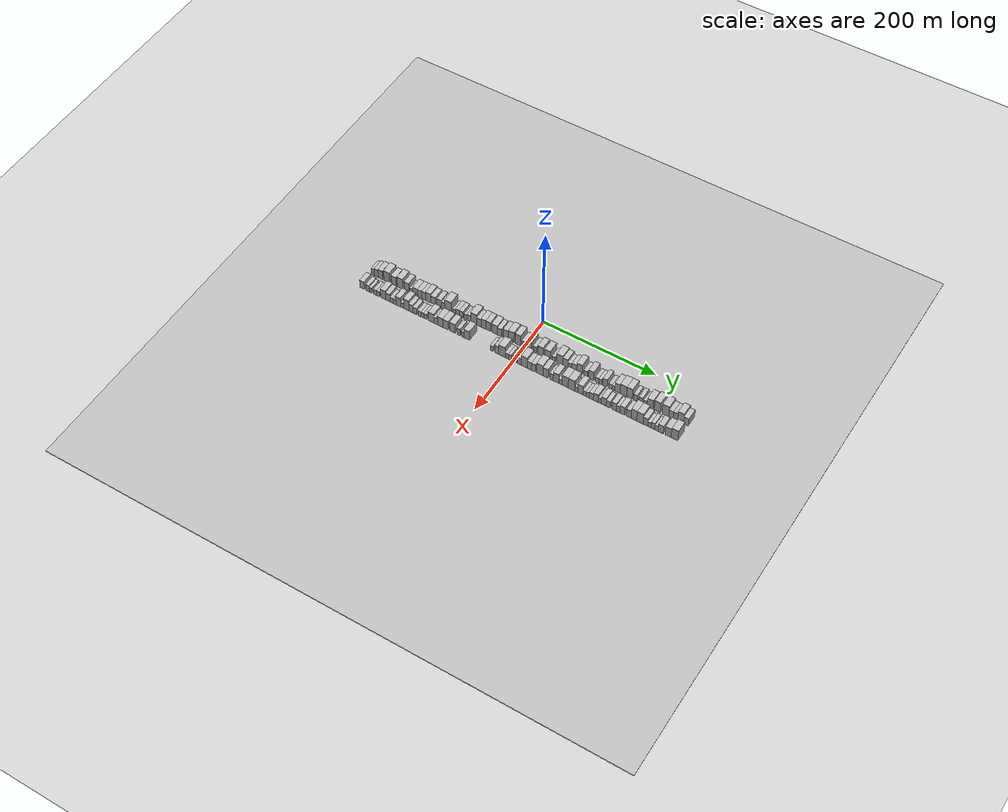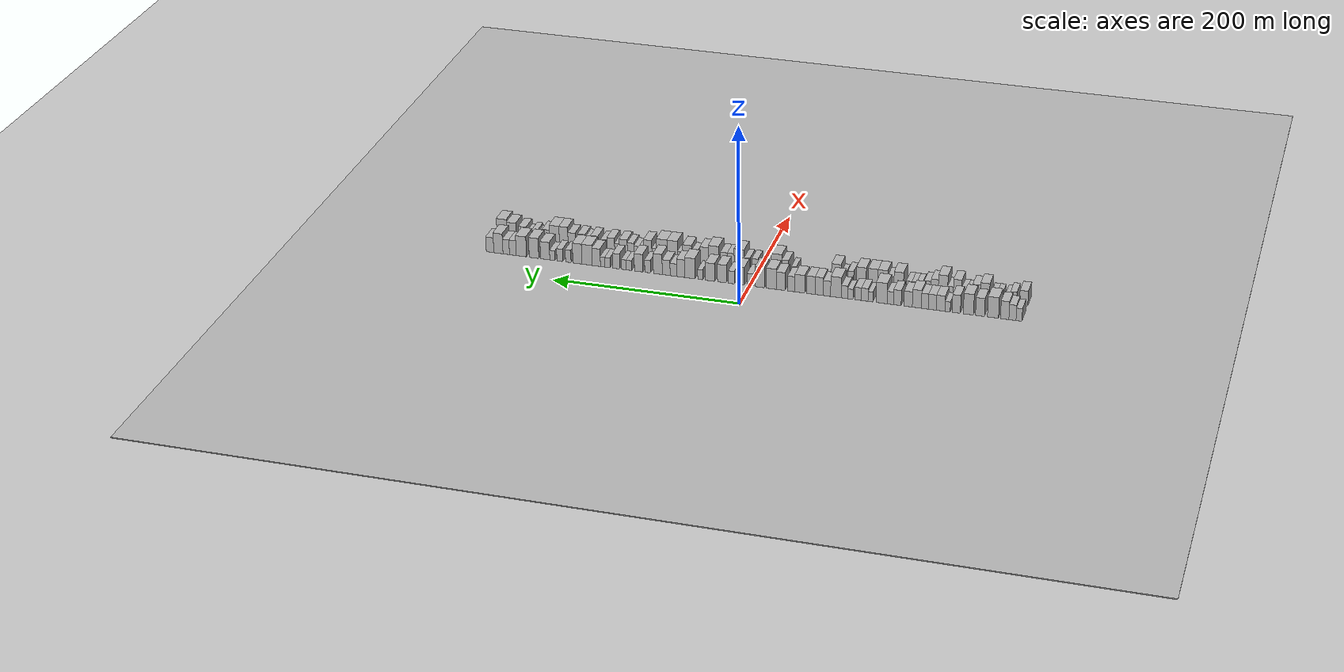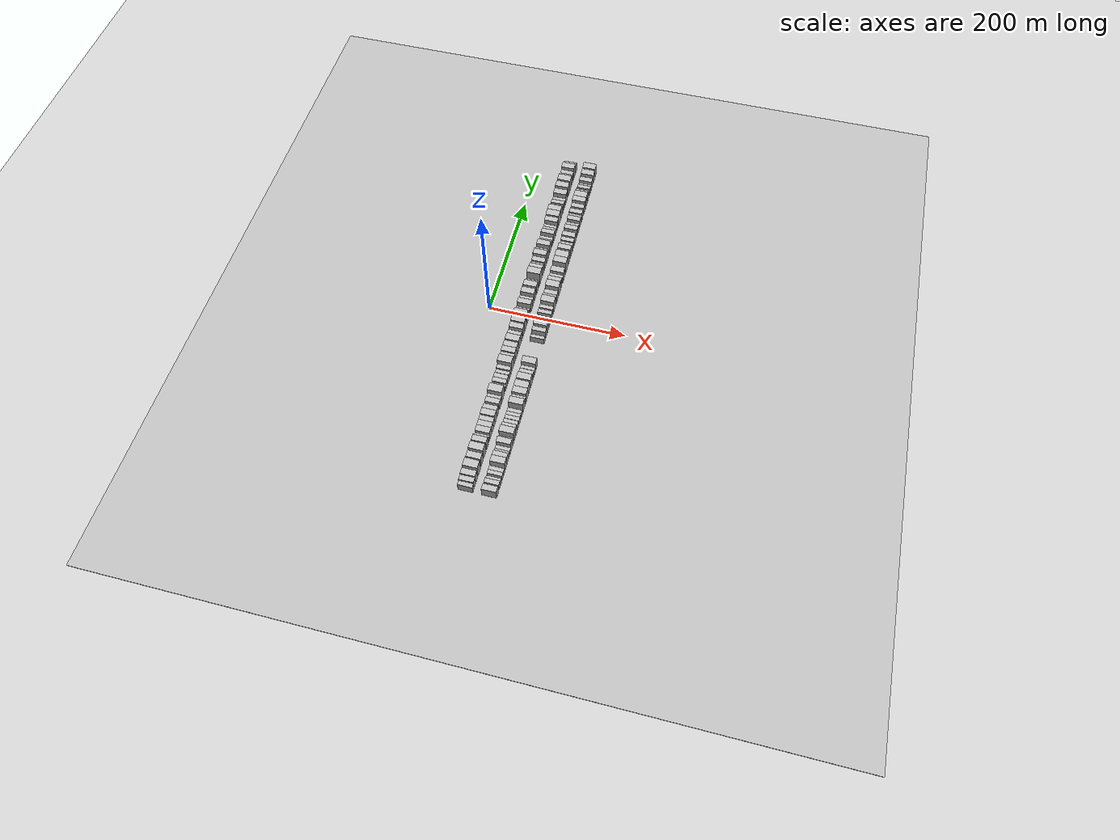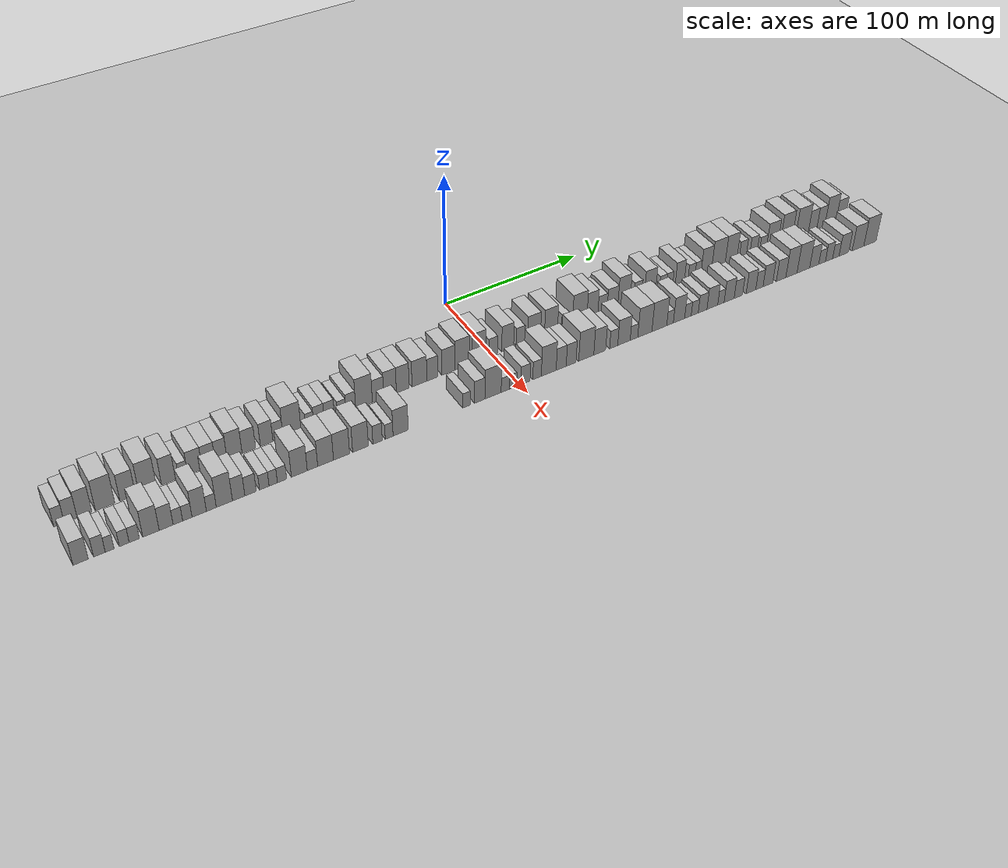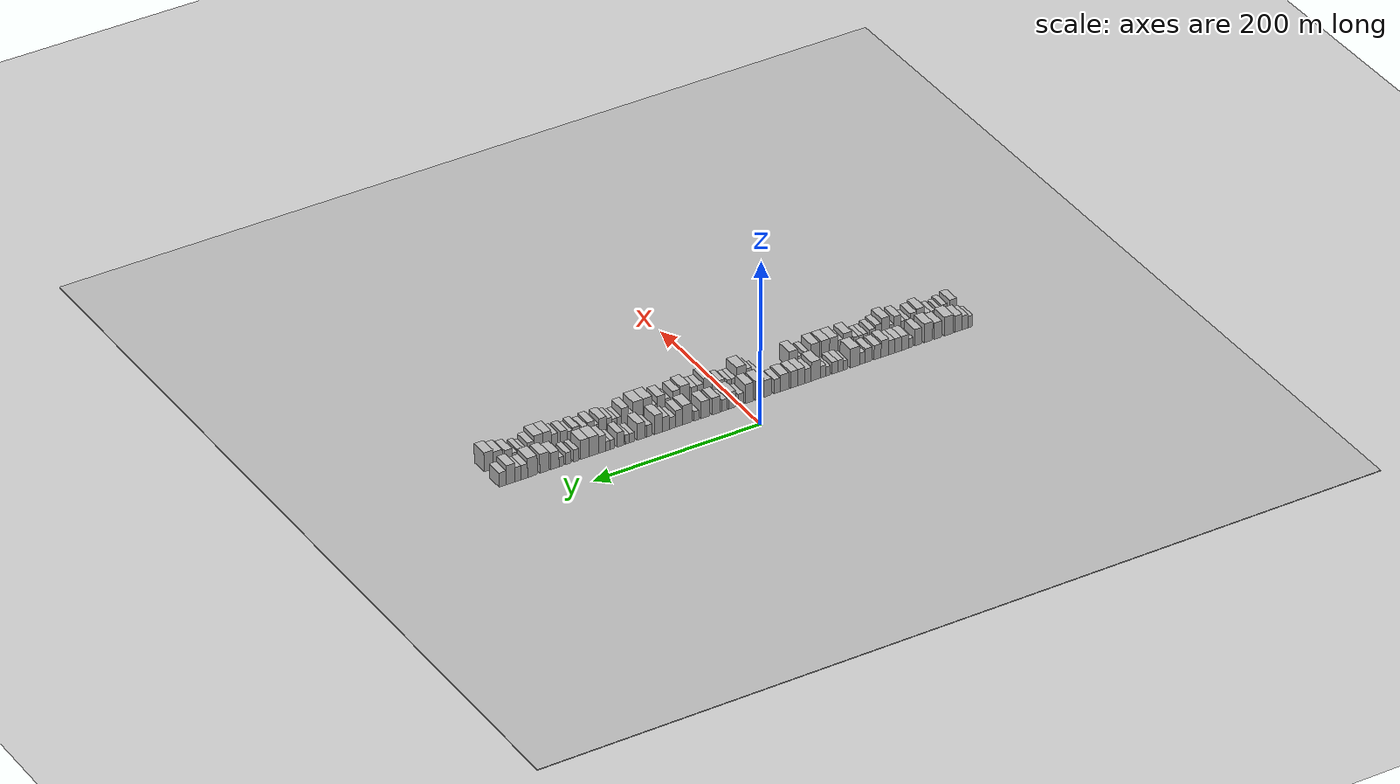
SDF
<?xml version="1.0" encoding="utf-8"?>

<sdf version="1.6">

   <world name="default">

      <gui fullscreen="0">

         <camera name="user_camera">

            <pose>-15 0 4.57585 0 0 0</pose>

            <view_controller>orbit</view_controller>

         </camera>

      </gui>

      <scene>

         <sky>

           <clouds>

             <speed>12</speed>

           </clouds>

         </sky>

         <ambient>0.4 0.4 0.4 1</ambient>

         <background>0.7 0.7 0.7 1</background>

         <shadows>1</shadows>

      </scene>

      <gravity>0 0 -9.8066</gravity>

      <magnetic_field>6e-06 2.3e-05 -4.2e-05</magnetic_field>

      <physics default="0" name="default_physics" type="ode">

         <ode>

            <solver>

               <type>quick</type>

               <iters>10</iters>

               <sor>1.0</sor>

               <use_dynamic_moi_rescaling>0</use_dynamic_moi_rescaling>

            </solver>

            <constraints>

               <cfm>0</cfm>

               <erp>0.2</erp>

               <contact_max_correcting_vel>100</contact_max_correcting_vel>

               <contact_surface_layer>0.001</contact_surface_layer>

            </constraints>

         </ode>

         <max_step_size>0.004</max_step_size>

         <real_time_factor>1</real_time_factor>

         <real_time_update_rate>250</real_time_update_rate>

      </physics>

      <light name="sun" type="directional">

         <cast_shadows>1</cast_shadows>

         <pose>0 0 10 0 0 0</pose>

         <diffuse>0.8 0.8 0.8 1</diffuse>

         <specular>0.2 0.2 0.2 1</specular>

         <attenuation>

            <range>1000</range>

            <constant>0.9</constant>

            <linear>0.01</linear>

            <quadratic>0.001</quadratic>

         </attenuation>

         <direction>-0.5 0.1 -0.9</direction>

      </light>

      <include>

         <name>ground_plane_1</name>

         <uri>model://HANNAS_ground_plane</uri>

         <pose>0 0 0  0 0 0</pose>

      </include>

      <include>

         <name>ground_plane_2</name>

         <uri>model://HANNAS_ground_plane</uri>

         <pose>100 0 0  0 0 0</pose>

      </include>

      <model name="building_1">

         <static>1</static>

         <pose frame="">50.0000 -280.9555 0 0.000000 0.000000 0.000000</pose>

         <link name="link">

            <pose frame="">0 0 7.50 0 0 0</pose>

            <collision name="collision">

               <geometry>

                  <box>

                     <size>20.0000 6.0890 15.0000</size>

                  </box>

               </geometry>

               <max_contacts>10</max_contacts>

               <surface>

                  <contact>

                     <ode/>

                  </contact>

                  <bounce/>

                  <friction>

                     <torsional>

                        <ode/>

                     </torsional>

                     <ode/>

                  </friction>

               </surface>

            </collision>

            <visual name="visual">

               <cast_shadows>0</cast_shadows>

               <geometry>

                  <box>

                     <size>20.0000 6.0890 15.0000</size>

                  </box>

               </geometry>

               <material>

                  <script>

                     <uri>model://HANNAS_wall/materials/scripts</uri>

                     <uri>model://HANNAS_wall/materials/textures</uri>

                     <name>vrc/HANNAS_wall</name>

                  </script>

               </material>

            </visual>

            <self_collide>0</self_collide>

            <enable_wind>0</enable_wind>

            <kinematic>0</kinematic>

         </link>

      </model>

      <model name="building_2">

         <static>1</static>

         <pose frame="">50.0000 -274.2463 0 0.000000 0.000000 0.000000</pose>

         <link name="link">

            <pose frame="">0 0 9.00 0 0 0</pose>

            <collision name="collision">

               <geometry>

                  <box>

                     <size>20.0000 7.3294 18.0000</size>

                  </box>

               </geometry>

               <max_contacts>10</max_contacts>

               <surface>

                  <contact>

                     <ode/>

                  </contact>

                  <bounce/>

                  <friction>

                     <torsional>

                        <ode/>

                     </torsional>

                     <ode/>

                  </friction>

               </surface>

            </collision>

            <visual name="visual">

               <cast_shadows>0</cast_shadows>

               <geometry>

                  <box>

                     <size>20.0000 7.3294 18.0000</size>

                  </box>

               </geometry>

               <material>

                  <script>

                     <uri>model://HANNAS_wall/materials/scripts</uri>

                     <uri>model://HANNAS_wall/materials/textures</uri>

                     <name>vrc/HANNAS_wall</name>

                  </script>

               </material>

            </visual>

            <self_collide>0</self_collide>

            <enable_wind>0</enable_wind>

            <kinematic>0</kinematic>

         </link>

      </model>

      <model name="building_3">

         <static>1</static>

         <pose frame="">50.0000 -266.2913 0 0.000000 0.000000 0.000000</pose>

         <link name="link">

            <pose frame="">0 0 10.50 0 0 0</pose>

            <collision name="collision">

               <geometry>

                  <box>

                     <size>20.0000 8.5806 21.0000</size>

                  </box>

               </geometry>

               <max_contacts>10</max_contacts>

               <surface>

                  <contact>

                     <ode/>

                  </contact>

                  <bounce/>

                  <friction>

                     <torsional>

                        <ode/>

                     </torsional>

                     <ode/>

                  </friction>

               </surface>

            </collision>

            <visual name="visual">

               <cast_shadows>0</cast_shadows>

               <geometry>

                  <box>

                     <size>20.0000 8.5806 21.0000</size>

                  </box>

               </geometry>

               <material>

                  <script>

                     <uri>model://HANNAS_wall/materials/scripts</uri>

                     <uri>model://HANNAS_wall/materials/textures</uri>

                     <name>vrc/HANNAS_wall</name>

                  </script>

               </material>

            </visual>

            <self_collide>0</self_collide>

            <enable_wind>0</enable_wind>

            <kinematic>0</kinematic>

         </link>

      </model>

      <model name="building_4">

         <static>1</static>

         <pose frame="">50.0000 -254.3090 0 0.000000 0.000000 0.000000</pose>

         <link name="link">

            <pose frame="">0 0 12.00 0 0 0</pose>

            <collision name="collision">

               <geometry>

                  <box>

                     <size>20.0000 11.3840 24.0000</size>

                  </box>

               </geometry>

               <max_contacts>10</max_contacts>

               <surface>

                  <contact>

                     <ode/>

                  </contact>

                  <bounce/>

                  <friction>

                     <torsional>

                        <ode/>

                     </torsional>

                     <ode/>

                  </friction>

               </surface>

            </collision>

            <visual name="visual">

               <cast_shadows>0</cast_shadows>

               <geometry>

                  <box>

                     <size>20.0000 11.3840 24.0000</size>

                  </box>

               </geometry>

               <material>

                  <script>

                     <uri>model://HANNAS_wall/materials/scripts</uri>

                     <uri>model://HANNAS_wall/materials/textures</uri>

                     <name>vrc/HANNAS_wall</name>

                  </script>

               </material>

            </visual>

            <self_collide>0</self_collide>

            <enable_wind>0</enable_wind>

            <kinematic>0</kinematic>

         </link>

      </model>

      <model name="building_5">

         <static>1</static>

         <pose frame="">50.0000 -240.9805 0 0.000000 0.000000 0.000000</pose>

         <link name="link">

            <pose frame="">0 0 10.50 0 0 0</pose>

            <collision name="collision">

               <geometry>

                  <box>

                     <size>20.0000 9.2729 21.0000</size>

                  </box>

               </geometry>

               <max_contacts>10</max_contacts>

               <surface>

                  <contact>

                     <ode/>

                  </contact>

                  <bounce/>

                  <friction>

                     <torsional>

                        <ode/>

                     </torsional>

                     <ode/>

                  </friction>

               </surface>

            </collision>

            <visual name="visual">

               <cast_shadows>0</cast_shadows>

               <geometry>

                  <box>

                     <size>20.0000 9.2729 21.0000</size>

                  </box>

               </geometry>

               <material>

                  <script>

                     <uri>model://HANNAS_wall/materials/scripts</uri>

                     <uri>model://HANNAS_wall/materials/textures</uri>

                     <name>vrc/HANNAS_wall</name>

                  </script>

               </material>

            </visual>

            <self_collide>0</self_collide>

            <enable_wind>0</enable_wind>

            <kinematic>0</kinematic>

         </link>

      </model>

      <model name="building_6">

         <static>1</static>

         <pose frame="">50.0000 -229.0669 0 0.000000 0.000000 0.000000</pose>

         <link name="link">

            <pose frame="">0 0 12.00 0 0 0</pose>

            <collision name="collision">

               <geometry>

                  <box>

                     <size>20.0000 10.5544 24.0000</size>

                  </box>

               </geometry>

               <max_contacts>10</max_contacts>

               <surface>

                  <contact>

                     <ode/>

                  </contact>

                  <bounce/>

                  <friction>

                     <torsional>

                        <ode/>

                     </torsional>

                     <ode/>

                  </friction>

               </surface>

            </collision>

            <visual name="visual">

               <cast_shadows>0</cast_shadows>

               <geometry>

                  <box>

                     <size>20.0000 10.5544 24.0000</size>

                  </box>

               </geometry>

               <material>

                  <script>

                     <uri>model://HANNAS_wall/materials/scripts</uri>

                     <uri>model://HANNAS_wall/materials/textures</uri>

                     <name>vrc/HANNAS_wall</name>

                  </script>

               </material>

            </visual>

            <self_collide>0</self_collide>

            <enable_wind>0</enable_wind>

            <kinematic>0</kinematic>

         </link>

      </model>

      <model name="building_7">

         <static>1</static>

         <pose frame="">50.0000 -216.5448 0 0.000000 0.000000 0.000000</pose>

         <link name="link">

            <pose frame="">0 0 10.50 0 0 0</pose>

            <collision name="collision">

               <geometry>

                  <box>

                     <size>20.0000 8.4898 21.0000</size>

                  </box>

               </geometry>

               <max_contacts>10</max_contacts>

               <surface>

                  <contact>

                     <ode/>

                  </contact>

                  <bounce/>

                  <friction>

                     <torsional>

                        <ode/>

                     </torsional>

                     <ode/>

                  </friction>

               </surface>

            </collision>

            <visual name="visual">

               <cast_shadows>0</cast_shadows>

               <geometry>

                  <box>

                     <size>20.0000 8.4898 21.0000</size>

                  </box>

               </geometry>

               <material>

                  <script>

                     <uri>model://HANNAS_wall/materials/scripts</uri>

                     <uri>model://HANNAS_wall/materials/textures</uri>

                     <name>vrc/HANNAS_wall</name>

                  </script>

               </material>

            </visual>

            <self_collide>0</self_collide>

            <enable_wind>0</enable_wind>

            <kinematic>0</kinematic>

         </link>

      </model>

      <model name="building_8">

         <static>1</static>

         <pose frame="">50.0000 -207.5800 0 0.000000 0.000000 0.000000</pose>

         <link name="link">

            <pose frame="">0 0 6.00 0 0 0</pose>

            <collision name="collision">

               <geometry>

                  <box>

                     <size>20.0000 5.4399 12.0000</size>

                  </box>

               </geometry>

               <max_contacts>10</max_contacts>

               <surface>

                  <contact>

                     <ode/>

                  </contact>

                  <bounce/>

                  <friction>

                     <torsional>

                        <ode/>

                     </torsional>

                     <ode/>

                  </friction>

               </surface>

            </collision>

            <visual name="visual">

               <cast_shadows>0</cast_shadows>

               <geometry>

                  <box>

                     <size>20.0000 5.4399 12.0000</size>

                  </box>

               </geometry>

               <material>

                  <script>

                     <uri>model://HANNAS_wall/materials/scripts</uri>

                     <uri>model://HANNAS_wall/materials/textures</uri>

                     <name>vrc/HANNAS_wall</name>

                  </script>

               </material>

            </visual>

            <self_collide>0</self_collide>

            <enable_wind>0</enable_wind>

            <kinematic>0</kinematic>

         </link>

      </model>

      <model name="building_9">

         <static>1</static>

         <pose frame="">50.0000 -200.3853 0 0.000000 0.000000 0.000000</pose>

         <link name="link">

            <pose frame="">0 0 9.00 0 0 0</pose>

            <collision name="collision">

               <geometry>

                  <box>

                     <size>20.0000 8.9496 18.0000</size>

                  </box>

               </geometry>

               <max_contacts>10</max_contacts>

               <surface>

                  <contact>

                     <ode/>

                  </contact>

                  <bounce/>

                  <friction>

                     <torsional>

                        <ode/>

                     </torsional>

                     <ode/>

                  </friction>

               </surface>

            </collision>

            <visual name="visual">

               <cast_shadows>0</cast_shadows>

               <geometry>

                  <box>

                     <size>20.0000 8.9496 18.0000</size>

                  </box>

               </geometry>

               <material>

                  <script>

                     <uri>model://HANNAS_wall/materials/scripts</uri>

                     <uri>model://HANNAS_wall/materials/textures</uri>

                     <name>vrc/HANNAS_wall</name>

                  </script>

               </material>

            </visual>

            <self_collide>0</self_collide>

            <enable_wind>0</enable_wind>

            <kinematic>0</kinematic>

         </link>

      </model>

      <model name="building_10">

         <static>1</static>

         <pose frame="">50.0000 -191.7918 0 0.000000 0.000000 0.000000</pose>

         <link name="link">

            <pose frame="">0 0 9.00 0 0 0</pose>

            <collision name="collision">

               <geometry>

                  <box>

                     <size>20.0000 8.2374 18.0000</size>

                  </box>

               </geometry>

               <max_contacts>10</max_contacts>

               <surface>

                  <contact>

                     <ode/>

                  </contact>

                  <bounce/>

                  <friction>

                     <torsional>

                        <ode/>

                     </torsional>

                     <ode/>

                  </friction>

               </surface>

            </collision>

            <visual name="visual">

               <cast_shadows>0</cast_shadows>

               <geometry>

                  <box>

                     <size>20.0000 8.2374 18.0000</size>

                  </box>

               </geometry>

               <material>

                  <script>

                     <uri>model://HANNAS_wall/materials/scripts</uri>

                     <uri>model://HANNAS_wall/materials/textures</uri>

                     <name>vrc/HANNAS_wall</name>

                  </script>

               </material>

            </visual>

            <self_collide>0</self_collide>

            <enable_wind>0</enable_wind>

            <kinematic>0</kinematic>

         </link>

      </model>

      <model name="building_11">

         <static>1</static>

         <pose frame="">50.0000 -184.0560 0 0.000000 0.000000 0.000000</pose>

         <link name="link">

            <pose frame="">0 0 9.00 0 0 0</pose>

            <collision name="collision">

               <geometry>

                  <box>

                     <size>20.0000 7.2342 18.0000</size>

                  </box>

               </geometry>

               <max_contacts>10</max_contacts>

               <surface>

                  <contact>

                     <ode/>

                  </contact>

                  <bounce/>

                  <friction>

                     <torsional>

                        <ode/>

                     </torsional>

                     <ode/>

                  </friction>

               </surface>

            </collision>

            <visual name="visual">

               <cast_shadows>0</cast_shadows>

               <geometry>

                  <box>

                     <size>20.0000 7.2342 18.0000</size>

                  </box>

               </geometry>

               <material>

                  <script>

                     <uri>model://HANNAS_wall/materials/scripts</uri>

                     <uri>model://HANNAS_wall/materials/textures</uri>

                     <name>vrc/HANNAS_wall</name>

                  </script>

               </material>

            </visual>

            <self_collide>0</self_collide>

            <enable_wind>0</enable_wind>

            <kinematic>0</kinematic>

         </link>

      </model>

      <model name="building_12">

         <static>1</static>

         <pose frame="">50.0000 -175.7094 0 0.000000 0.000000 0.000000</pose>

         <link name="link">

            <pose frame="">0 0 10.50 0 0 0</pose>

            <collision name="collision">

               <geometry>

                  <box>

                     <size>20.0000 9.4589 21.0000</size>

                  </box>

               </geometry>

               <max_contacts>10</max_contacts>

               <surface>

                  <contact>

                     <ode/>

                  </contact>

                  <bounce/>

                  <friction>

                     <torsional>

                        <ode/>

                     </torsional>

                     <ode/>

                  </friction>

               </surface>

            </collision>

            <visual name="visual">

               <cast_shadows>0</cast_shadows>

               <geometry>

                  <box>

                     <size>20.0000 9.4589 21.0000</size>

                  </box>

               </geometry>

               <material>

                  <script>

                     <uri>model://HANNAS_wall/materials/scripts</uri>

                     <uri>model://HANNAS_wall/materials/textures</uri>

                     <name>vrc/HANNAS_wall</name>

                  </script>

               </material>

            </visual>

            <self_collide>0</self_collide>

            <enable_wind>0</enable_wind>

            <kinematic>0</kinematic>

         </link>

      </model>

      <model name="building_13">

         <static>1</static>

         <pose frame="">50.0000 -166.6836 0 0.000000 0.000000 0.000000</pose>

         <link name="link">

            <pose frame="">0 0 9.00 0 0 0</pose>

            <collision name="collision">

               <geometry>

                  <box>

                     <size>20.0000 8.5927 18.0000</size>

                  </box>

               </geometry>

               <max_contacts>10</max_contacts>

               <surface>

                  <contact>

                     <ode/>

                  </contact>

                  <bounce/>

                  <friction>

                     <torsional>

                        <ode/>

                     </torsional>

                     <ode/>

                  </friction>

               </surface>

            </collision>

            <visual name="visual">

               <cast_shadows>0</cast_shadows>

               <geometry>

                  <box>

                     <size>20.0000 8.5927 18.0000</size>

                  </box>

               </geometry>

               <material>

                  <script>

                     <uri>model://HANNAS_wall/materials/scripts</uri>

                     <uri>model://HANNAS_wall/materials/textures</uri>

                     <name>vrc/HANNAS_wall</name>

                  </script>

               </material>

            </visual>

            <self_collide>0</self_collide>

            <enable_wind>0</enable_wind>

            <kinematic>0</kinematic>

         </link>

      </model>

      <model name="building_14">

         <static>1</static>

         <pose frame="">50.0000 -155.3409 0 0.000000 0.000000 0.000000</pose>

         <link name="link">

            <pose frame="">0 0 9.00 0 0 0</pose>

            <collision name="collision">

               <geometry>

                  <box>

                     <size>20.0000 8.0925 18.0000</size>

                  </box>

               </geometry>

               <max_contacts>10</max_contacts>

               <surface>

                  <contact>

                     <ode/>

                  </contact>

                  <bounce/>

                  <friction>

                     <torsional>

                        <ode/>

                     </torsional>

                     <ode/>

                  </friction>

               </surface>

            </collision>

            <visual name="visual">

               <cast_shadows>0</cast_shadows>

               <geometry>

                  <box>

                     <size>20.0000 8.0925 18.0000</size>

                  </box>

               </geometry>

               <material>

                  <script>

                     <uri>model://HANNAS_wall/materials/scripts</uri>

                     <uri>model://HANNAS_wall/materials/textures</uri>

                     <name>vrc/HANNAS_wall</name>

                  </script>

               </material>

            </visual>

            <self_collide>0</self_collide>

            <enable_wind>0</enable_wind>

            <kinematic>0</kinematic>

         </link>

      </model>

      <model name="building_15">

         <static>1</static>

         <pose frame="">50.0000 -148.0356 0 0.000000 0.000000 0.000000</pose>

         <link name="link">

            <pose frame="">0 0 7.50 0 0 0</pose>

            <collision name="collision">

               <geometry>

                  <box>

                     <size>20.0000 6.5181 15.0000</size>

                  </box>

               </geometry>

               <max_contacts>10</max_contacts>

               <surface>

                  <contact>

                     <ode/>

                  </contact>

                  <bounce/>

                  <friction>

                     <torsional>

                        <ode/>

                     </torsional>

                     <ode/>

                  </friction>

               </surface>

            </collision>

            <visual name="visual">

               <cast_shadows>0</cast_shadows>

               <geometry>

                  <box>

                     <size>20.0000 6.5181 15.0000</size>

                  </box>

               </geometry>

               <material>

                  <script>

                     <uri>model://HANNAS_wall/materials/scripts</uri>

                     <uri>model://HANNAS_wall/materials/textures</uri>

                     <name>vrc/HANNAS_wall</name>

                  </script>

               </material>

            </visual>

            <self_collide>0</self_collide>

            <enable_wind>0</enable_wind>

            <kinematic>0</kinematic>

         </link>

      </model>

      <model name="building_16">

         <static>1</static>

         <pose frame="">50.0000 -138.9039 0 0.000000 0.000000 0.000000</pose>

         <link name="link">

            <pose frame="">0 0 12.00 0 0 0</pose>

            <collision name="collision">

               <geometry>

                  <box>

                     <size>20.0000 11.7452 24.0000</size>

                  </box>

               </geometry>

               <max_contacts>10</max_contacts>

               <surface>

                  <contact>

                     <ode/>

                  </contact>

                  <bounce/>

                  <friction>

                     <torsional>

                        <ode/>

                     </torsional>

                     <ode/>

                  </friction>

               </surface>

            </collision>

            <visual name="visual">

               <cast_shadows>0</cast_shadows>

               <geometry>

                  <box>

                     <size>20.0000 11.7452 24.0000</size>

                  </box>

               </geometry>

               <material>

                  <script>

                     <uri>model://HANNAS_wall/materials/scripts</uri>

                     <uri>model://HANNAS_wall/materials/textures</uri>

                     <name>vrc/HANNAS_wall</name>

                  </script>

               </material>

            </visual>

            <self_collide>0</self_collide>

            <enable_wind>0</enable_wind>

            <kinematic>0</kinematic>

         </link>

      </model>

      <model name="building_17">

         <static>1</static>

         <pose frame="">50.0000 -127.3835 0 0.000000 0.000000 0.000000</pose>

         <link name="link">

            <pose frame="">0 0 6.00 0 0 0</pose>

            <collision name="collision">

               <geometry>

                  <box>

                     <size>20.0000 5.2957 12.0000</size>

                  </box>

               </geometry>

               <max_contacts>10</max_contacts>

               <surface>

                  <contact>

                     <ode/>

                  </contact>

                  <bounce/>

                  <friction>

                     <torsional>

                        <ode/>

                     </torsional>

                     <ode/>

                  </friction>

               </surface>

            </collision>

            <visual name="visual">

               <cast_shadows>0</cast_shadows>

               <geometry>

                  <box>

                     <size>20.0000 5.2957 12.0000</size>

                  </box>

               </geometry>

               <material>

                  <script>

                     <uri>model://HANNAS_wall/materials/scripts</uri>

                     <uri>model://HANNAS_wall/materials/textures</uri>

                     <name>vrc/HANNAS_wall</name>

                  </script>

               </material>

            </visual>

            <self_collide>0</self_collide>

            <enable_wind>0</enable_wind>

            <kinematic>0</kinematic>

         </link>

      </model>

      <model name="building_18">

         <static>1</static>

         <pose frame="">50.0000 -121.2496 0 0.000000 0.000000 0.000000</pose>

         <link name="link">

            <pose frame="">0 0 7.50 0 0 0</pose>

            <collision name="collision">

               <geometry>

                  <box>

                     <size>20.0000 6.9722 15.0000</size>

                  </box>

               </geometry>

               <max_contacts>10</max_contacts>

               <surface>

                  <contact>

                     <ode/>

                  </contact>

                  <bounce/>

                  <friction>

                     <torsional>

                        <ode/>

                     </torsional>

                     <ode/>

                  </friction>

               </surface>

            </collision>

            <visual name="visual">

               <cast_shadows>0</cast_shadows>

               <geometry>

                  <box>

                     <size>20.0000 6.9722 15.0000</size>

                  </box>

               </geometry>

               <material>

                  <script>

                     <uri>model://HANNAS_wall/materials/scripts</uri>

                     <uri>model://HANNAS_wall/materials/textures</uri>

                     <name>vrc/HANNAS_wall</name>

                  </script>

               </material>

            </visual>

            <self_collide>0</self_collide>

            <enable_wind>0</enable_wind>

            <kinematic>0</kinematic>

         </link>

      </model>

      <model name="building_19">

         <static>1</static>

         <pose frame="">50.0000 -114.3665 0 0.000000 0.000000 0.000000</pose>

         <link name="link">

            <pose frame="">0 0 7.50 0 0 0</pose>

            <collision name="collision">

               <geometry>

                  <box>

                     <size>20.0000 6.7938 15.0000</size>

                  </box>

               </geometry>

               <max_contacts>10</max_contacts>

               <surface>

                  <contact>

                     <ode/>

                  </contact>

                  <bounce/>

                  <friction>

                     <torsional>

                        <ode/>

                     </torsional>

                     <ode/>

                  </friction>

               </surface>

            </collision>

            <visual name="visual">

               <cast_shadows>0</cast_shadows>

               <geometry>

                  <box>

                     <size>20.0000 6.7938 15.0000</size>

                  </box>

               </geometry>

               <material>

                  <script>

                     <uri>model://HANNAS_wall/materials/scripts</uri>

                     <uri>model://HANNAS_wall/materials/textures</uri>

                     <name>vrc/HANNAS_wall</name>

                  </script>

               </material>

            </visual>

            <self_collide>0</self_collide>

            <enable_wind>0</enable_wind>

            <kinematic>0</kinematic>

         </link>

      </model>

      <model name="building_20">

         <static>1</static>

         <pose frame="">50.0000 -106.2062 0 0.000000 0.000000 0.000000</pose>

         <link name="link">

            <pose frame="">0 0 6.00 0 0 0</pose>

            <collision name="collision">

               <geometry>

                  <box>

                     <size>20.0000 5.5269 12.0000</size>

                  </box>

               </geometry>

               <max_contacts>10</max_contacts>

               <surface>

                  <contact>

                     <ode/>

                  </contact>

                  <bounce/>

                  <friction>

                     <torsional>

                        <ode/>

                     </torsional>

                     <ode/>

                  </friction>

               </surface>

            </collision>

            <visual name="visual">

               <cast_shadows>0</cast_shadows>

               <geometry>

                  <box>

                     <size>20.0000 5.5269 12.0000</size>

                  </box>

               </geometry>

               <material>

                  <script>

                     <uri>model://HANNAS_wall/materials/scripts</uri>

                     <uri>model://HANNAS_wall/materials/textures</uri>

                     <name>vrc/HANNAS_wall</name>

                  </script>

               </material>

            </visual>

            <self_collide>0</self_collide>

            <enable_wind>0</enable_wind>

            <kinematic>0</kinematic>

         </link>

      </model>

      <model name="building_21">

         <static>1</static>

         <pose frame="">50.0000 -100.1263 0 0.000000 0.000000 0.000000</pose>

         <link name="link">

            <pose frame="">0 0 7.50 0 0 0</pose>

            <collision name="collision">

               <geometry>

                  <box>

                     <size>20.0000 6.6329 15.0000</size>

                  </box>

               </geometry>

               <max_contacts>10</max_contacts>

               <surface>

                  <contact>

                     <ode/>

                  </contact>

                  <bounce/>

                  <friction>

                     <torsional>

                        <ode/>

                     </torsional>

                     <ode/>

                  </friction>

               </surface>

            </collision>

            <visual name="visual">

               <cast_shadows>0</cast_shadows>

               <geometry>

                  <box>

                     <size>20.0000 6.6329 15.0000</size>

                  </box>

               </geometry>

               <material>

                  <script>

                     <uri>model://HANNAS_wall/materials/scripts</uri>

                     <uri>model://HANNAS_wall/materials/textures</uri>

                     <name>vrc/HANNAS_wall</name>

                  </script>

               </material>

            </visual>

            <self_collide>0</self_collide>

            <enable_wind>0</enable_wind>

            <kinematic>0</kinematic>

         </link>

      </model>

      <model name="building_22">

         <static>1</static>

         <pose frame="">50.0000 -91.1507 0 0.000000 0.000000 0.000000</pose>

         <link name="link">

            <pose frame="">0 0 12.00 0 0 0</pose>

            <collision name="collision">

               <geometry>

                  <box>

                     <size>20.0000 11.3184 24.0000</size>

                  </box>

               </geometry>

               <max_contacts>10</max_contacts>

               <surface>

                  <contact>

                     <ode/>

                  </contact>

                  <bounce/>

                  <friction>

                     <torsional>

                        <ode/>

                     </torsional>

                     <ode/>

                  </friction>

               </surface>

            </collision>

            <visual name="visual">

               <cast_shadows>0</cast_shadows>

               <geometry>

                  <box>

                     <size>20.0000 11.3184 24.0000</size>

                  </box>

               </geometry>

               <material>

                  <script>

                     <uri>model://HANNAS_wall/materials/scripts</uri>

                     <uri>model://HANNAS_wall/materials/textures</uri>

                     <name>vrc/HANNAS_wall</name>

                  </script>

               </material>

            </visual>

            <self_collide>0</self_collide>

            <enable_wind>0</enable_wind>

            <kinematic>0</kinematic>

         </link>

      </model>

      <model name="building_23">

         <static>1</static>

         <pose frame="">50.0000 -81.5928 0 0.000000 0.000000 0.000000</pose>

         <link name="link">

            <pose frame="">0 0 9.00 0 0 0</pose>

            <collision name="collision">

               <geometry>

                  <box>

                     <size>20.0000 7.7973 18.0000</size>

                  </box>

               </geometry>

               <max_contacts>10</max_contacts>

               <surface>

                  <contact>

                     <ode/>

                  </contact>

                  <bounce/>

                  <friction>

                     <torsional>

                        <ode/>

                     </torsional>

                     <ode/>

                  </friction>

               </surface>

            </collision>

            <visual name="visual">

               <cast_shadows>0</cast_shadows>

               <geometry>

                  <box>

                     <size>20.0000 7.7973 18.0000</size>

                  </box>

               </geometry>

               <material>

                  <script>

                     <uri>model://HANNAS_wall/materials/scripts</uri>

                     <uri>model://HANNAS_wall/materials/textures</uri>

                     <name>vrc/HANNAS_wall</name>

                  </script>

               </material>

            </visual>

            <self_collide>0</self_collide>

            <enable_wind>0</enable_wind>

            <kinematic>0</kinematic>

         </link>

      </model>

      <model name="building_24">

         <static>1</static>

         <pose frame="">50.0000 -73.3543 0 0.000000 0.000000 0.000000</pose>

         <link name="link">

            <pose frame="">0 0 10.50 0 0 0</pose>

            <collision name="collision">

               <geometry>

                  <box>

                     <size>20.0000 8.6798 21.0000</size>

                  </box>

               </geometry>

               <max_contacts>10</max_contacts>

               <surface>

                  <contact>

                     <ode/>

                  </contact>

                  <bounce/>

                  <friction>

                     <torsional>

                        <ode/>

                     </torsional>

                     <ode/>

                  </friction>

               </surface>

            </collision>

            <visual name="visual">

               <cast_shadows>0</cast_shadows>

               <geometry>

                  <box>

                     <size>20.0000 8.6798 21.0000</size>

                  </box>

               </geometry>

               <material>

                  <script>

                     <uri>model://HANNAS_wall/materials/scripts</uri>

                     <uri>model://HANNAS_wall/materials/textures</uri>

                     <name>vrc/HANNAS_wall</name>

                  </script>

               </material>

            </visual>

            <self_collide>0</self_collide>

            <enable_wind>0</enable_wind>

            <kinematic>0</kinematic>

         </link>

      </model>

      <model name="building_25">

         <static>1</static>

         <pose frame="">50.0000 -64.5917 0 0.000000 0.000000 0.000000</pose>

         <link name="link">

            <pose frame="">0 0 10.50 0 0 0</pose>

            <collision name="collision">

               <geometry>

                  <box>

                     <size>20.0000 8.8454 21.0000</size>

                  </box>

               </geometry>

               <max_contacts>10</max_contacts>

               <surface>

                  <contact>

                     <ode/>

                  </contact>

                  <bounce/>

                  <friction>

                     <torsional>

                        <ode/>

                     </torsional>

                     <ode/>

                  </friction>

               </surface>

            </collision>

            <visual name="visual">

               <cast_shadows>0</cast_shadows>

               <geometry>

                  <box>

                     <size>20.0000 8.8454 21.0000</size>

                  </box>

               </geometry>

               <material>

                  <script>

                     <uri>model://HANNAS_wall/materials/scripts</uri>

                     <uri>model://HANNAS_wall/materials/textures</uri>

                     <name>vrc/HANNAS_wall</name>

                  </script>

               </material>

            </visual>

            <self_collide>0</self_collide>

            <enable_wind>0</enable_wind>

            <kinematic>0</kinematic>

         </link>

      </model>

      <model name="building_26">

         <static>1</static>

         <pose frame="">50.0000 -52.9582 0 0.000000 0.000000 0.000000</pose>

         <link name="link">

            <pose frame="">0 0 10.50 0 0 0</pose>

            <collision name="collision">

               <geometry>

                  <box>

                     <size>20.0000 10.4217 21.0000</size>

                  </box>

               </geometry>

               <max_contacts>10</max_contacts>

               <surface>

                  <contact>

                     <ode/>

                  </contact>

                  <bounce/>

                  <friction>

                     <torsional>

                        <ode/>

                     </torsional>

                     <ode/>

                  </friction>

               </surface>

            </collision>

            <visual name="visual">

               <cast_shadows>0</cast_shadows>

               <geometry>

                  <box>

                     <size>20.0000 10.4217 21.0000</size>

                  </box>

               </geometry>

               <material>

                  <script>

                     <uri>model://HANNAS_wall/materials/scripts</uri>

                     <uri>model://HANNAS_wall/materials/textures</uri>

                     <name>vrc/HANNAS_wall</name>

                  </script>

               </material>

            </visual>

            <self_collide>0</self_collide>

            <enable_wind>0</enable_wind>

            <kinematic>0</kinematic>

         </link>

      </model>

      <model name="building_27">

         <static>1</static>

         <pose frame="">50.0000 -43.9188 0 0.000000 0.000000 0.000000</pose>

         <link name="link">

            <pose frame="">0 0 9.00 0 0 0</pose>

            <collision name="collision">

               <geometry>

                  <box>

                     <size>20.0000 7.6571 18.0000</size>

                  </box>

               </geometry>

               <max_contacts>10</max_contacts>

               <surface>

                  <contact>

                     <ode/>

                  </contact>

                  <bounce/>

                  <friction>

                     <torsional>

                        <ode/>

                     </torsional>

                     <ode/>

                  </friction>

               </surface>

            </collision>

            <visual name="visual">

               <cast_shadows>0</cast_shadows>

               <geometry>

                  <box>

                     <size>20.0000 7.6571 18.0000</size>

                  </box>

               </geometry>

               <material>

                  <script>

                     <uri>model://HANNAS_wall/materials/scripts</uri>

                     <uri>model://HANNAS_wall/materials/textures</uri>

                     <name>vrc/HANNAS_wall</name>

                  </script>

               </material>

            </visual>

            <self_collide>0</self_collide>

            <enable_wind>0</enable_wind>

            <kinematic>0</kinematic>

         </link>

      </model>

      <model name="building_28">

         <static>1</static>

         <pose frame="">50.0000 -32.5424 0 0.000000 0.000000 0.000000</pose>

         <link name="link">

            <pose frame="">0 0 10.50 0 0 0</pose>

            <collision name="collision">

               <geometry>

                  <box>

                     <size>20.0000 9.0957 21.0000</size>

                  </box>

               </geometry>

               <max_contacts>10</max_contacts>

               <surface>

                  <contact>

                     <ode/>

                  </contact>

                  <bounce/>

                  <friction>

                     <torsional>

                        <ode/>

                     </torsional>

                     <ode/>

                  </friction>

               </surface>

            </collision>

            <visual name="visual">

               <cast_shadows>0</cast_shadows>

               <geometry>

                  <box>

                     <size>20.0000 9.0957 21.0000</size>

                  </box>

               </geometry>

               <material>

                  <script>

                     <uri>model://HANNAS_wall/materials/scripts</uri>

                     <uri>model://HANNAS_wall/materials/textures</uri>

                     <name>vrc/HANNAS_wall</name>

                  </script>

               </material>

            </visual>

            <self_collide>0</self_collide>

            <enable_wind>0</enable_wind>

            <kinematic>0</kinematic>

         </link>

      </model>

      <model name="building_29">

         <static>1</static>

         <pose frame="">50.0000 -22.6621 0 0.000000 0.000000 0.000000</pose>

         <link name="link">

            <pose frame="">0 0 12.00 0 0 0</pose>

            <collision name="collision">

               <geometry>

                  <box>

                     <size>20.0000 10.6648 24.0000</size>

                  </box>

               </geometry>

               <max_contacts>10</max_contacts>

               <surface>

                  <contact>

                     <ode/>

                  </contact>

                  <bounce/>

                  <friction>

                     <torsional>

                        <ode/>

                     </torsional>

                     <ode/>

                  </friction>

               </surface>

            </collision>

            <visual name="visual">

               <cast_shadows>0</cast_shadows>

               <geometry>

                  <box>

                     <size>20.0000 10.6648 24.0000</size>

                  </box>

               </geometry>

               <material>

                  <script>

                     <uri>model://HANNAS_wall/materials/scripts</uri>

                     <uri>model://HANNAS_wall/materials/textures</uri>

                     <name>vrc/HANNAS_wall</name>

                  </script>

               </material>

            </visual>

            <self_collide>0</self_collide>

            <enable_wind>0</enable_wind>

            <kinematic>0</kinematic>

         </link>

      </model>

      <model name="building_30">

         <static>1</static>

         <pose frame="">50.0000 -10.3878 0 0.000000 0.000000 0.000000</pose>

         <link name="link">

            <pose frame="">0 0 12.00 0 0 0</pose>

            <collision name="collision">

               <geometry>

                  <box>

                     <size>20.0000 9.8838 24.0000</size>

                  </box>

               </geometry>

               <max_contacts>10</max_contacts>

               <surface>

                  <contact>

                     <ode/>

                  </contact>

                  <bounce/>

                  <friction>

                     <torsional>

                        <ode/>

                     </torsional>

                     <ode/>

                  </friction>

               </surface>

            </collision>

            <visual name="visual">

               <cast_shadows>0</cast_shadows>

               <geometry>

                  <box>

                     <size>20.0000 9.8838 24.0000</size>

                  </box>

               </geometry>

               <material>

                  <script>

                     <uri>model://HANNAS_wall/materials/scripts</uri>

                     <uri>model://HANNAS_wall/materials/textures</uri>

                     <name>vrc/HANNAS_wall</name>

                  </script>

               </material>

            </visual>

            <self_collide>0</self_collide>

            <enable_wind>0</enable_wind>

            <kinematic>0</kinematic>

         </link>

      </model>

      <model name="building_31">

         <static>1</static>

         <pose frame="">50.0000 -0.1809 0 0.000000 0.000000 0.000000</pose>

         <link name="link">

            <pose frame="">0 0 7.50 0 0 0</pose>

            <collision name="collision">

               <geometry>

                  <box>

                     <size>20.0000 6.5299 15.0000</size>

                  </box>

               </geometry>

               <max_contacts>10</max_contacts>

               <surface>

                  <contact>

                     <ode/>

                  </contact>

                  <bounce/>

                  <friction>

                     <torsional>

                        <ode/>

                     </torsional>

                     <ode/>

                  </friction>

               </surface>

            </collision>

            <visual name="visual">

               <cast_shadows>0</cast_shadows>

               <geometry>

                  <box>

                     <size>20.0000 6.5299 15.0000</size>

                  </box>

               </geometry>

               <material>

                  <script>

                     <uri>model://HANNAS_wall/materials/scripts</uri>

                     <uri>model://HANNAS_wall/materials/textures</uri>

                     <name>vrc/HANNAS_wall</name>

                  </script>

               </material>

            </visual>

            <self_collide>0</self_collide>

            <enable_wind>0</enable_wind>

            <kinematic>0</kinematic>

         </link>

      </model>

      <model name="building_32">

         <static>1</static>

         <pose frame="">50.0000 10.4703 0 0.000000 0.000000 0.000000</pose>

         <link name="link">

            <pose frame="">0 0 10.50 0 0 0</pose>

            <collision name="collision">

               <geometry>

                  <box>

                     <size>20.0000 8.7726 21.0000</size>

                  </box>

               </geometry>

               <max_contacts>10</max_contacts>

               <surface>

                  <contact>

                     <ode/>

                  </contact>

                  <bounce/>

                  <friction>

                     <torsional>

                        <ode/>

                     </torsional>

                     <ode/>

                  </friction>

               </surface>

            </collision>

            <visual name="visual">

               <cast_shadows>0</cast_shadows>

               <geometry>

                  <box>

                     <size>20.0000 8.7726 21.0000</size>

                  </box>

               </geometry>

               <material>

                  <script>

                     <uri>model://HANNAS_wall/materials/scripts</uri>

                     <uri>model://HANNAS_wall/materials/textures</uri>

                     <name>vrc/HANNAS_wall</name>

                  </script>

               </material>

            </visual>

            <self_collide>0</self_collide>

            <enable_wind>0</enable_wind>

            <kinematic>0</kinematic>

         </link>

      </model>

      <model name="building_33">

         <static>1</static>

         <pose frame="">50.0000 20.0780 0 0.000000 0.000000 0.000000</pose>

         <link name="link">

            <pose frame="">0 0 7.50 0 0 0</pose>

            <collision name="collision">

               <geometry>

                  <box>

                     <size>20.0000 6.4428 15.0000</size>

                  </box>

               </geometry>

               <max_contacts>10</max_contacts>

               <surface>

                  <contact>

                     <ode/>

                  </contact>

                  <bounce/>

                  <friction>

                     <torsional>

                        <ode/>

                     </torsional>

                     <ode/>

                  </friction>

               </surface>

            </collision>

            <visual name="visual">

               <cast_shadows>0</cast_shadows>

               <geometry>

                  <box>

                     <size>20.0000 6.4428 15.0000</size>

                  </box>

               </geometry>

               <material>

                  <script>

                     <uri>model://HANNAS_wall/materials/scripts</uri>

                     <uri>model://HANNAS_wall/materials/textures</uri>

                     <name>vrc/HANNAS_wall</name>

                  </script>

               </material>

            </visual>

            <self_collide>0</self_collide>

            <enable_wind>0</enable_wind>

            <kinematic>0</kinematic>

         </link>

      </model>

      <model name="building_34">

         <static>1</static>

         <pose frame="">50.0000 30.1253 0 0.000000 0.000000 0.000000</pose>

         <link name="link">

            <pose frame="">0 0 10.50 0 0 0</pose>

            <collision name="collision">

               <geometry>

                  <box>

                     <size>20.0000 9.6518 21.0000</size>

                  </box>

               </geometry>

               <max_contacts>10</max_contacts>

               <surface>

                  <contact>

                     <ode/>

                  </contact>

                  <bounce/>

                  <friction>

                     <torsional>

                        <ode/>

                     </torsional>

                     <ode/>

                  </friction>

               </surface>

            </collision>

            <visual name="visual">

               <cast_shadows>0</cast_shadows>

               <geometry>

                  <box>

                     <size>20.0000 9.6518 21.0000</size>

                  </box>

               </geometry>

               <material>

                  <script>

                     <uri>model://HANNAS_wall/materials/scripts</uri>

                     <uri>model://HANNAS_wall/materials/textures</uri>

                     <name>vrc/HANNAS_wall</name>

                  </script>

               </material>

            </visual>

            <self_collide>0</self_collide>

            <enable_wind>0</enable_wind>

            <kinematic>0</kinematic>

         </link>

      </model>

      <model name="building_35">

         <static>1</static>

         <pose frame="">50.0000 42.9140 0 0.000000 0.000000 0.000000</pose>

         <link name="link">

            <pose frame="">0 0 10.50 0 0 0</pose>

            <collision name="collision">

               <geometry>

                  <box>

                     <size>20.0000 9.9255 21.0000</size>

                  </box>

               </geometry>

               <max_contacts>10</max_contacts>

               <surface>

                  <contact>

                     <ode/>

                  </contact>

                  <bounce/>

                  <friction>

                     <torsional>

                        <ode/>

                     </torsional>

                     <ode/>

                  </friction>

               </surface>

            </collision>

            <visual name="visual">

               <cast_shadows>0</cast_shadows>

               <geometry>

                  <box>

                     <size>20.0000 9.9255 21.0000</size>

                  </box>

               </geometry>

               <material>

                  <script>

                     <uri>model://HANNAS_wall/materials/scripts</uri>

                     <uri>model://HANNAS_wall/materials/textures</uri>

                     <name>vrc/HANNAS_wall</name>

                  </script>

               </material>

            </visual>

            <self_collide>0</self_collide>

            <enable_wind>0</enable_wind>

            <kinematic>0</kinematic>

         </link>

      </model>

      <model name="building_36">

         <static>1</static>

         <pose frame="">50.0000 53.5680 0 0.000000 0.000000 0.000000</pose>

         <link name="link">

            <pose frame="">0 0 6.00 0 0 0</pose>

            <collision name="collision">

               <geometry>

                  <box>

                     <size>20.0000 5.3825 12.0000</size>

                  </box>

               </geometry>

               <max_contacts>10</max_contacts>

               <surface>

                  <contact>

                     <ode/>

                  </contact>

                  <bounce/>

                  <friction>

                     <torsional>

                        <ode/>

                     </torsional>

                     <ode/>

                  </friction>

               </surface>

            </collision>

            <visual name="visual">

               <cast_shadows>0</cast_shadows>

               <geometry>

                  <box>

                     <size>20.0000 5.3825 12.0000</size>

                  </box>

               </geometry>

               <material>

                  <script>

                     <uri>model://HANNAS_wall/materials/scripts</uri>

                     <uri>model://HANNAS_wall/materials/textures</uri>

                     <name>vrc/HANNAS_wall</name>

                  </script>

               </material>

            </visual>

            <self_collide>0</self_collide>

            <enable_wind>0</enable_wind>

            <kinematic>0</kinematic>

         </link>

      </model>

      <model name="building_37">

         <static>1</static>

         <pose frame="">50.0000 64.8389 0 0.000000 0.000000 0.000000</pose>

         <link name="link">

            <pose frame="">0 0 12.00 0 0 0</pose>

            <collision name="collision">

               <geometry>

                  <box>

                     <size>20.0000 11.1592 24.0000</size>

                  </box>

               </geometry>

               <max_contacts>10</max_contacts>

               <surface>

                  <contact>

                     <ode/>

                  </contact>

                  <bounce/>

                  <friction>

                     <torsional>

                        <ode/>

                     </torsional>

                     <ode/>

                  </friction>

               </surface>

            </collision>

            <visual name="visual">

               <cast_shadows>0</cast_shadows>

               <geometry>

                  <box>

                     <size>20.0000 11.1592 24.0000</size>

                  </box>

               </geometry>

               <material>

                  <script>

                     <uri>model://HANNAS_wall/materials/scripts</uri>

                     <uri>model://HANNAS_wall/materials/textures</uri>

                     <name>vrc/HANNAS_wall</name>

                  </script>

               </material>

            </visual>

            <self_collide>0</self_collide>

            <enable_wind>0</enable_wind>

            <kinematic>0</kinematic>

         </link>

      </model>

      <model name="building_38">

         <static>1</static>

         <pose frame="">50.0000 74.6822 0 0.000000 0.000000 0.000000</pose>

         <link name="link">

            <pose frame="">0 0 10.50 0 0 0</pose>

            <collision name="collision">

               <geometry>

                  <box>

                     <size>20.0000 8.5273 21.0000</size>

                  </box>

               </geometry>

               <max_contacts>10</max_contacts>

               <surface>

                  <contact>

                     <ode/>

                  </contact>

                  <bounce/>

                  <friction>

                     <torsional>

                        <ode/>

                     </torsional>

                     <ode/>

                  </friction>

               </surface>

            </collision>

            <visual name="visual">

               <cast_shadows>0</cast_shadows>

               <geometry>

                  <box>

                     <size>20.0000 8.5273 21.0000</size>

                  </box>

               </geometry>

               <material>

                  <script>

                     <uri>model://HANNAS_wall/materials/scripts</uri>

                     <uri>model://HANNAS_wall/materials/textures</uri>

                     <name>vrc/HANNAS_wall</name>

                  </script>

               </material>

            </visual>

            <self_collide>0</self_collide>

            <enable_wind>0</enable_wind>

            <kinematic>0</kinematic>

         </link>

      </model>

      <model name="building_39">

         <static>1</static>

         <pose frame="">50.0000 82.5390 0 0.000000 0.000000 0.000000</pose>

         <link name="link">

            <pose frame="">0 0 7.50 0 0 0</pose>

            <collision name="collision">

               <geometry>

                  <box>

                     <size>20.0000 7.1863 15.0000</size>

                  </box>

               </geometry>

               <max_contacts>10</max_contacts>

               <surface>

                  <contact>

                     <ode/>

                  </contact>

                  <bounce/>

                  <friction>

                     <torsional>

                        <ode/>

                     </torsional>

                     <ode/>

                  </friction>

               </surface>

            </collision>

            <visual name="visual">

               <cast_shadows>0</cast_shadows>

               <geometry>

                  <box>

                     <size>20.0000 7.1863 15.0000</size>

                  </box>

               </geometry>

               <material>

                  <script>

                     <uri>model://HANNAS_wall/materials/scripts</uri>

                     <uri>model://HANNAS_wall/materials/textures</uri>

                     <name>vrc/HANNAS_wall</name>

                  </script>

               </material>

            </visual>

            <self_collide>0</self_collide>

            <enable_wind>0</enable_wind>

            <kinematic>0</kinematic>

         </link>

      </model>

      <model name="building_40">

         <static>1</static>

         <pose frame="">50.0000 90.3806 0 0.000000 0.000000 0.000000</pose>

         <link name="link">

            <pose frame="">0 0 9.00 0 0 0</pose>

            <collision name="collision">

               <geometry>

                  <box>

                     <size>20.0000 8.4969 18.0000</size>

                  </box>

               </geometry>

               <max_contacts>10</max_contacts>

               <surface>

                  <contact>

                     <ode/>

                  </contact>

                  <bounce/>

                  <friction>

                     <torsional>

                        <ode/>

                     </torsional>

                     <ode/>

                  </friction>

               </surface>

            </collision>

            <visual name="visual">

               <cast_shadows>0</cast_shadows>

               <geometry>

                  <box>

                     <size>20.0000 8.4969 18.0000</size>

                  </box>

               </geometry>

               <material>

                  <script>

                     <uri>model://HANNAS_wall/materials/scripts</uri>

                     <uri>model://HANNAS_wall/materials/textures</uri>

                     <name>vrc/HANNAS_wall</name>

                  </script>

               </material>

            </visual>

            <self_collide>0</self_collide>

            <enable_wind>0</enable_wind>

            <kinematic>0</kinematic>

         </link>

      </model>

      <model name="building_41">

         <static>1</static>

         <pose frame="">50.0000 99.4449 0 0.000000 0.000000 0.000000</pose>

         <link name="link">

            <pose frame="">0 0 12.00 0 0 0</pose>

            <collision name="collision">

               <geometry>

                  <box>

                     <size>20.0000 9.6316 24.0000</size>

                  </box>

               </geometry>

               <max_contacts>10</max_contacts>

               <surface>

                  <contact>

                     <ode/>

                  </contact>

                  <bounce/>

                  <friction>

                     <torsional>

                        <ode/>

                     </torsional>

                     <ode/>

                  </friction>

               </surface>

            </collision>

            <visual name="visual">

               <cast_shadows>0</cast_shadows>

               <geometry>

                  <box>

                     <size>20.0000 9.6316 24.0000</size>

                  </box>

               </geometry>

               <material>

                  <script>

                     <uri>model://HANNAS_wall/materials/scripts</uri>

                     <uri>model://HANNAS_wall/materials/textures</uri>

                     <name>vrc/HANNAS_wall</name>

                  </script>

               </material>

            </visual>

            <self_collide>0</self_collide>

            <enable_wind>0</enable_wind>

            <kinematic>0</kinematic>

         </link>

      </model>

      <model name="building_42">

         <static>1</static>

         <pose frame="">50.0000 110.4633 0 0.000000 0.000000 0.000000</pose>

         <link name="link">

            <pose frame="">0 0 7.50 0 0 0</pose>

            <collision name="collision">

               <geometry>

                  <box>

                     <size>20.0000 6.4053 15.0000</size>

                  </box>

               </geometry>

               <max_contacts>10</max_contacts>

               <surface>

                  <contact>

                     <ode/>

                  </contact>

                  <bounce/>

                  <friction>

                     <torsional>

                        <ode/>

                     </torsional>

                     <ode/>

                  </friction>

               </surface>

            </collision>

            <visual name="visual">

               <cast_shadows>0</cast_shadows>

               <geometry>

                  <box>

                     <size>20.0000 6.4053 15.0000</size>

                  </box>

               </geometry>

               <material>

                  <script>

                     <uri>model://HANNAS_wall/materials/scripts</uri>

                     <uri>model://HANNAS_wall/materials/textures</uri>

                     <name>vrc/HANNAS_wall</name>

                  </script>

               </material>

            </visual>

            <self_collide>0</self_collide>

            <enable_wind>0</enable_wind>

            <kinematic>0</kinematic>

         </link>

      </model>

      <model name="building_43">

         <static>1</static>

         <pose frame="">50.0000 120.2700 0 0.000000 0.000000 0.000000</pose>

         <link name="link">

            <pose frame="">0 0 10.50 0 0 0</pose>

            <collision name="collision">

               <geometry>

                  <box>

                     <size>20.0000 9.2081 21.0000</size>

                  </box>

               </geometry>

               <max_contacts>10</max_contacts>

               <surface>

                  <contact>

                     <ode/>

                  </contact>

                  <bounce/>

                  <friction>

                     <torsional>

                        <ode/>

                     </torsional>

                     <ode/>

                  </friction>

               </surface>

            </collision>

            <visual name="visual">

               <cast_shadows>0</cast_shadows>

               <geometry>

                  <box>

                     <size>20.0000 9.2081 21.0000</size>

                  </box>

               </geometry>

               <material>

                  <script>

                     <uri>model://HANNAS_wall/materials/scripts</uri>

                     <uri>model://HANNAS_wall/materials/textures</uri>

                     <name>vrc/HANNAS_wall</name>

                  </script>

               </material>

            </visual>

            <self_collide>0</self_collide>

            <enable_wind>0</enable_wind>

            <kinematic>0</kinematic>

         </link>

      </model>

      <model name="building_44">

         <static>1</static>

         <pose frame="">50.0000 130.8555 0 0.000000 0.000000 0.000000</pose>

         <link name="link">

            <pose frame="">0 0 6.00 0 0 0</pose>

            <collision name="collision">

               <geometry>

                  <box>

                     <size>20.0000 5.9628 12.0000</size>

                  </box>

               </geometry>

               <max_contacts>10</max_contacts>

               <surface>

                  <contact>

                     <ode/>

                  </contact>

                  <bounce/>

                  <friction>

                     <torsional>

                        <ode/>

                     </torsional>

                     <ode/>

                  </friction>

               </surface>

            </collision>

            <visual name="visual">

               <cast_shadows>0</cast_shadows>

               <geometry>

                  <box>

                     <size>20.0000 5.9628 12.0000</size>

                  </box>

               </geometry>

               <material>

                  <script>

                     <uri>model://HANNAS_wall/materials/scripts</uri>

                     <uri>model://HANNAS_wall/materials/textures</uri>

                     <name>vrc/HANNAS_wall</name>

                  </script>

               </material>

            </visual>

            <self_collide>0</self_collide>

            <enable_wind>0</enable_wind>

            <kinematic>0</kinematic>

         </link>

      </model>

      <model name="building_45">

         <static>1</static>

         <pose frame="">50.0000 136.3919 0 0.000000 0.000000 0.000000</pose>

         <link name="link">

            <pose frame="">0 0 6.00 0 0 0</pose>

            <collision name="collision">

               <geometry>

                  <box>

                     <size>20.0000 5.1102 12.0000</size>

                  </box>

               </geometry>

               <max_contacts>10</max_contacts>

               <surface>

                  <contact>

                     <ode/>

                  </contact>

                  <bounce/>

                  <friction>

                     <torsional>

                        <ode/>

                     </torsional>

                     <ode/>

                  </friction>

               </surface>

            </collision>

            <visual name="visual">

               <cast_shadows>0</cast_shadows>

               <geometry>

                  <box>

                     <size>20.0000 5.1102 12.0000</size>

                  </box>

               </geometry>

               <material>

                  <script>

                     <uri>model://HANNAS_wall/materials/scripts</uri>

                     <uri>model://HANNAS_wall/materials/textures</uri>

                     <name>vrc/HANNAS_wall</name>

                  </script>

               </material>

            </visual>

            <self_collide>0</self_collide>

            <enable_wind>0</enable_wind>

            <kinematic>0</kinematic>

         </link>

      </model>

      <model name="building_46">

         <static>1</static>

         <pose frame="">50.0000 144.7280 0 0.000000 0.000000 0.000000</pose>

         <link name="link">

            <pose frame="">0 0 9.00 0 0 0</pose>

            <collision name="collision">

               <geometry>

                  <box>

                     <size>20.0000 7.5619 18.0000</size>

                  </box>

               </geometry>

               <max_contacts>10</max_contacts>

               <surface>

                  <contact>

                     <ode/>

                  </contact>

                  <bounce/>

                  <friction>

                     <torsional>

                        <ode/>

                     </torsional>

                     <ode/>

                  </friction>

               </surface>

            </collision>

            <visual name="visual">

               <cast_shadows>0</cast_shadows>

               <geometry>

                  <box>

                     <size>20.0000 7.5619 18.0000</size>

                  </box>

               </geometry>

               <material>

                  <script>

                     <uri>model://HANNAS_wall/materials/scripts</uri>

                     <uri>model://HANNAS_wall/materials/textures</uri>

                     <name>vrc/HANNAS_wall</name>

                  </script>

               </material>

            </visual>

            <self_collide>0</self_collide>

            <enable_wind>0</enable_wind>

            <kinematic>0</kinematic>

         </link>

      </model>

      <model name="building_47">

         <static>1</static>

         <pose frame="">50.0000 154.3621 0 0.000000 0.000000 0.000000</pose>

         <link name="link">

            <pose frame="">0 0 6.00 0 0 0</pose>

            <collision name="collision">

               <geometry>

                  <box>

                     <size>20.0000 5.7063 12.0000</size>

                  </box>

               </geometry>

               <max_contacts>10</max_contacts>

               <surface>

                  <contact>

                     <ode/>

                  </contact>

                  <bounce/>

                  <friction>

                     <torsional>

                        <ode/>

                     </torsional>

                     <ode/>

                  </friction>

               </surface>

            </collision>

            <visual name="visual">

               <cast_shadows>0</cast_shadows>

               <geometry>

                  <box>

                     <size>20.0000 5.7063 12.0000</size>

                  </box>

               </geometry>

               <material>

                  <script>

                     <uri>model://HANNAS_wall/materials/scripts</uri>

                     <uri>model://HANNAS_wall/materials/textures</uri>

                     <name>vrc/HANNAS_wall</name>

                  </script>

               </material>

            </visual>

            <self_collide>0</self_collide>

            <enable_wind>0</enable_wind>

            <kinematic>0</kinematic>

         </link>

      </model>

      <model name="building_48">

         <static>1</static>

         <pose frame="">50.0000 159.6737 0 0.000000 0.000000 0.000000</pose>

         <link name="link">

            <pose frame="">0 0 6.00 0 0 0</pose>

            <collision name="collision">

               <geometry>

                  <box>

                     <size>20.0000 4.9170 12.0000</size>

                  </box>

               </geometry>

               <max_contacts>10</max_contacts>

               <surface>

                  <contact>

                     <ode/>

                  </contact>

                  <bounce/>

                  <friction>

                     <torsional>

                        <ode/>

                     </torsional>

                     <ode/>

                  </friction>

               </surface>

            </collision>

            <visual name="visual">

               <cast_shadows>0</cast_shadows>

               <geometry>

                  <box>

                     <size>20.0000 4.9170 12.0000</size>

                  </box>

               </geometry>

               <material>

                  <script>

                     <uri>model://HANNAS_wall/materials/scripts</uri>

                     <uri>model://HANNAS_wall/materials/textures</uri>

                     <name>vrc/HANNAS_wall</name>

                  </script>

               </material>

            </visual>

            <self_collide>0</self_collide>

            <enable_wind>0</enable_wind>

            <kinematic>0</kinematic>

         </link>

      </model>

      <model name="building_49">

         <static>1</static>

         <pose frame="">50.0000 166.6061 0 0.000000 0.000000 0.000000</pose>

         <link name="link">

            <pose frame="">0 0 10.50 0 0 0</pose>

            <collision name="collision">

               <geometry>

                  <box>

                     <size>20.0000 8.9478 21.0000</size>

                  </box>

               </geometry>

               <max_contacts>10</max_contacts>

               <surface>

                  <contact>

                     <ode/>

                  </contact>

                  <bounce/>

                  <friction>

                     <torsional>

                        <ode/>

                     </torsional>

                     <ode/>

                  </friction>

               </surface>

            </collision>

            <visual name="visual">

               <cast_shadows>0</cast_shadows>

               <geometry>

                  <box>

                     <size>20.0000 8.9478 21.0000</size>

                  </box>

               </geometry>

               <material>

                  <script>

                     <uri>model://HANNAS_wall/materials/scripts</uri>

                     <uri>model://HANNAS_wall/materials/textures</uri>

                     <name>vrc/HANNAS_wall</name>

                  </script>

               </material>

            </visual>

            <self_collide>0</self_collide>

            <enable_wind>0</enable_wind>

            <kinematic>0</kinematic>

         </link>

      </model>

      <model name="building_50">

         <static>1</static>

         <pose frame="">50.0000 176.7668 0 0.000000 0.000000 0.000000</pose>

         <link name="link">

            <pose frame="">0 0 12.00 0 0 0</pose>

            <collision name="collision">

               <geometry>

                  <box>

                     <size>20.0000 11.3736 24.0000</size>

                  </box>

               </geometry>

               <max_contacts>10</max_contacts>

               <surface>

                  <contact>

                     <ode/>

                  </contact>

                  <bounce/>

                  <friction>

                     <torsional>

                        <ode/>

                     </torsional>

                     <ode/>

                  </friction>

               </surface>

            </collision>

            <visual name="visual">

               <cast_shadows>0</cast_shadows>

               <geometry>

                  <box>

                     <size>20.0000 11.3736 24.0000</size>

                  </box>

               </geometry>

               <material>

                  <script>

                     <uri>model://HANNAS_wall/materials/scripts</uri>

                     <uri>model://HANNAS_wall/materials/textures</uri>

                     <name>vrc/HANNAS_wall</name>

                  </script>

               </material>

            </visual>

            <self_collide>0</self_collide>

            <enable_wind>0</enable_wind>

            <kinematic>0</kinematic>

         </link>

      </model>

      <model name="building_51">

         <static>1</static>

         <pose frame="">50.0000 187.4327 0 0.000000 0.000000 0.000000</pose>

         <link name="link">

            <pose frame="">0 0 12.00 0 0 0</pose>

            <collision name="collision">

               <geometry>

                  <box>

                     <size>20.0000 9.9584 24.0000</size>

                  </box>

               </geometry>

               <max_contacts>10</max_contacts>

               <surface>

                  <contact>

                     <ode/>

                  </contact>

                  <bounce/>

                  <friction>

                     <torsional>

                        <ode/>

                     </torsional>

                     <ode/>

                  </friction>

               </surface>

            </collision>

            <visual name="visual">

               <cast_shadows>0</cast_shadows>

               <geometry>

                  <box>

                     <size>20.0000 9.9584 24.0000</size>

                  </box>

               </geometry>

               <material>

                  <script>

                     <uri>model://HANNAS_wall/materials/scripts</uri>

                     <uri>model://HANNAS_wall/materials/textures</uri>

                     <name>vrc/HANNAS_wall</name>

                  </script>

               </material>

            </visual>

            <self_collide>0</self_collide>

            <enable_wind>0</enable_wind>

            <kinematic>0</kinematic>

         </link>

      </model>

      <model name="building_52">

         <static>1</static>

         <pose frame="">50.0000 197.4578 0 0.000000 0.000000 0.000000</pose>

         <link name="link">

            <pose frame="">0 0 7.50 0 0 0</pose>

            <collision name="collision">

               <geometry>

                  <box>

                     <size>20.0000 6.0918 15.0000</size>

                  </box>

               </geometry>

               <max_contacts>10</max_contacts>

               <surface>

                  <contact>

                     <ode/>

                  </contact>

                  <bounce/>

                  <friction>

                     <torsional>

                        <ode/>

                     </torsional>

                     <ode/>

                  </friction>

               </surface>

            </collision>

            <visual name="visual">

               <cast_shadows>0</cast_shadows>

               <geometry>

                  <box>

                     <size>20.0000 6.0918 15.0000</size>

                  </box>

               </geometry>

               <material>

                  <script>

                     <uri>model://HANNAS_wall/materials/scripts</uri>

                     <uri>model://HANNAS_wall/materials/textures</uri>

                     <name>vrc/HANNAS_wall</name>

                  </script>

               </material>

            </visual>

            <self_collide>0</self_collide>

            <enable_wind>0</enable_wind>

            <kinematic>0</kinematic>

         </link>

      </model>

      <model name="building_53">

         <static>1</static>

         <pose frame="">50.0000 206.7702 0 0.000000 0.000000 0.000000</pose>

         <link name="link">

            <pose frame="">0 0 7.50 0 0 0</pose>

            <collision name="collision">

               <geometry>

                  <box>

                     <size>20.0000 6.5331 15.0000</size>

                  </box>

               </geometry>

               <max_contacts>10</max_contacts>

               <surface>

                  <contact>

                     <ode/>

                  </contact>

                  <bounce/>

                  <friction>

                     <torsional>

                        <ode/>

                     </torsional>

                     <ode/>

                  </friction>

               </surface>

            </collision>

            <visual name="visual">

               <cast_shadows>0</cast_shadows>

               <geometry>

                  <box>

                     <size>20.0000 6.5331 15.0000</size>

                  </box>

               </geometry>

               <material>

                  <script>

                     <uri>model://HANNAS_wall/materials/scripts</uri>

                     <uri>model://HANNAS_wall/materials/textures</uri>

                     <name>vrc/HANNAS_wall</name>

                  </script>

               </material>

            </visual>

            <self_collide>0</self_collide>

            <enable_wind>0</enable_wind>

            <kinematic>0</kinematic>

         </link>

      </model>

      <model name="building_54">

         <static>1</static>

         <pose frame="">50.0000 214.9954 0 0.000000 0.000000 0.000000</pose>

         <link name="link">

            <pose frame="">0 0 6.00 0 0 0</pose>

            <collision name="collision">

               <geometry>

                  <box>

                     <size>20.0000 5.9171 12.0000</size>

                  </box>

               </geometry>

               <max_contacts>10</max_contacts>

               <surface>

                  <contact>

                     <ode/>

                  </contact>

                  <bounce/>

                  <friction>

                     <torsional>

                        <ode/>

                     </torsional>

                     <ode/>

                  </friction>

               </surface>

            </collision>

            <visual name="visual">

               <cast_shadows>0</cast_shadows>

               <geometry>

                  <box>

                     <size>20.0000 5.9171 12.0000</size>

                  </box>

               </geometry>

               <material>

                  <script>

                     <uri>model://HANNAS_wall/materials/scripts</uri>

                     <uri>model://HANNAS_wall/materials/textures</uri>

                     <name>vrc/HANNAS_wall</name>

                  </script>

               </material>

            </visual>

            <self_collide>0</self_collide>

            <enable_wind>0</enable_wind>

            <kinematic>0</kinematic>

         </link>

      </model>

      <model name="building_55">

         <static>1</static>

         <pose frame="">50.0000 223.0476 0 0.000000 0.000000 0.000000</pose>

         <link name="link">

            <pose frame="">0 0 10.50 0 0 0</pose>

            <collision name="collision">

               <geometry>

                  <box>

                     <size>20.0000 10.1874 21.0000</size>

                  </box>

               </geometry>

               <max_contacts>10</max_contacts>

               <surface>

                  <contact>

                     <ode/>

                  </contact>

                  <bounce/>

                  <friction>

                     <torsional>

                        <ode/>

                     </torsional>

                     <ode/>

                  </friction>

               </surface>

            </collision>

            <visual name="visual">

               <cast_shadows>0</cast_shadows>

               <geometry>

                  <box>

                     <size>20.0000 10.1874 21.0000</size>

                  </box>

               </geometry>

               <material>

                  <script>

                     <uri>model://HANNAS_wall/materials/scripts</uri>

                     <uri>model://HANNAS_wall/materials/textures</uri>

                     <name>vrc/HANNAS_wall</name>

                  </script>

               </material>

            </visual>

            <self_collide>0</self_collide>

            <enable_wind>0</enable_wind>

            <kinematic>0</kinematic>

         </link>

      </model>

      <model name="building_56">

         <static>1</static>

         <pose frame="">50.0000 235.4307 0 0.000000 0.000000 0.000000</pose>

         <link name="link">

            <pose frame="">0 0 12.00 0 0 0</pose>

            <collision name="collision">

               <geometry>

                  <box>

                     <size>20.0000 10.5788 24.0000</size>

                  </box>

               </geometry>

               <max_contacts>10</max_contacts>

               <surface>

                  <contact>

                     <ode/>

                  </contact>

                  <bounce/>

                  <friction>

                     <torsional>

                        <ode/>

                     </torsional>

                     <ode/>

                  </friction>

               </surface>

            </collision>

            <visual name="visual">

               <cast_shadows>0</cast_shadows>

               <geometry>

                  <box>

                     <size>20.0000 10.5788 24.0000</size>

                  </box>

               </geometry>

               <material>

                  <script>

                     <uri>model://HANNAS_wall/materials/scripts</uri>

                     <uri>model://HANNAS_wall/materials/textures</uri>

                     <name>vrc/HANNAS_wall</name>

                  </script>

               </material>

            </visual>

            <self_collide>0</self_collide>

            <enable_wind>0</enable_wind>

            <kinematic>0</kinematic>

         </link>

      </model>

      <model name="building_57">

         <static>1</static>

         <pose frame="">50.0000 249.4549 0 0.000000 0.000000 0.000000</pose>

         <link name="link">

            <pose frame="">0 0 12.00 0 0 0</pose>

            <collision name="collision">

               <geometry>

                  <box>

                     <size>20.0000 11.4696 24.0000</size>

                  </box>

               </geometry>

               <max_contacts>10</max_contacts>

               <surface>

                  <contact>

                     <ode/>

                  </contact>

                  <bounce/>

                  <friction>

                     <torsional>

                        <ode/>

                     </torsional>

                     <ode/>

                  </friction>

               </surface>

            </collision>

            <visual name="visual">

               <cast_shadows>0</cast_shadows>

               <geometry>

                  <box>

                     <size>20.0000 11.4696 24.0000</size>

                  </box>

               </geometry>

               <material>

                  <script>

                     <uri>model://HANNAS_wall/materials/scripts</uri>

                     <uri>model://HANNAS_wall/materials/textures</uri>

                     <name>vrc/HANNAS_wall</name>

                  </script>

               </material>

            </visual>

            <self_collide>0</self_collide>

            <enable_wind>0</enable_wind>

            <kinematic>0</kinematic>

         </link>

      </model>

      <model name="building_58">

         <static>1</static>

         <pose frame="">50.0000 258.9614 0 0.000000 0.000000 0.000000</pose>

         <link name="link">

            <pose frame="">0 0 9.00 0 0 0</pose>

            <collision name="collision">

               <geometry>

                  <box>

                     <size>20.0000 7.5433 18.0000</size>

                  </box>

               </geometry>

               <max_contacts>10</max_contacts>

               <surface>

                  <contact>

                     <ode/>

                  </contact>

                  <bounce/>

                  <friction>

                     <torsional>

                        <ode/>

                     </torsional>

                     <ode/>

                  </friction>

               </surface>

            </collision>

            <visual name="visual">

               <cast_shadows>0</cast_shadows>

               <geometry>

                  <box>

                     <size>20.0000 7.5433 18.0000</size>

                  </box>

               </geometry>

               <material>

                  <script>

                     <uri>model://HANNAS_wall/materials/scripts</uri>

                     <uri>model://HANNAS_wall/materials/textures</uri>

                     <name>vrc/HANNAS_wall</name>

                  </script>

               </material>

            </visual>

            <self_collide>0</self_collide>

            <enable_wind>0</enable_wind>

            <kinematic>0</kinematic>

         </link>

      </model>

      <model name="building_59">

         <static>1</static>

         <pose frame="">50.0000 266.3637 0 0.000000 0.000000 0.000000</pose>

         <link name="link">

            <pose frame="">0 0 9.00 0 0 0</pose>

            <collision name="collision">

               <geometry>

                  <box>

                     <size>20.0000 7.2614 18.0000</size>

                  </box>

               </geometry>

               <max_contacts>10</max_contacts>

               <surface>

                  <contact>

                     <ode/>

                  </contact>

                  <bounce/>

                  <friction>

                     <torsional>

                        <ode/>

                     </torsional>

                     <ode/>

                  </friction>

               </surface>

            </collision>

            <visual name="visual">

               <cast_shadows>0</cast_shadows>

               <geometry>

                  <box>

                     <size>20.0000 7.2614 18.0000</size>

                  </box>

               </geometry>

               <material>

                  <script>

                     <uri>model://HANNAS_wall/materials/scripts</uri>

                     <uri>model://HANNAS_wall/materials/textures</uri>

                     <name>vrc/HANNAS_wall</name>

                  </script>

               </material>

            </visual>

            <self_collide>0</self_collide>

            <enable_wind>0</enable_wind>

            <kinematic>0</kinematic>

         </link>

      </model>

      <model name="building_60">

         <static>1</static>

         <pose frame="">50.0000 275.0978 0 0.000000 0.000000 0.000000</pose>

         <link name="link">

            <pose frame="">0 0 12.00 0 0 0</pose>

            <collision name="collision">

               <geometry>

                  <box>

                     <size>20.0000 10.2068 24.0000</size>

                  </box>

               </geometry>

               <max_contacts>10</max_contacts>

               <surface>

                  <contact>

                     <ode/>

                  </contact>

                  <bounce/>

                  <friction>

                     <torsional>

                        <ode/>

                     </torsional>

                     <ode/>

                  </friction>

               </surface>

            </collision>

            <visual name="visual">

               <cast_shadows>0</cast_shadows>

               <geometry>

                  <box>

                     <size>20.0000 10.2068 24.0000</size>

                  </box>

               </geometry>

               <material>

                  <script>

                     <uri>model://HANNAS_wall/materials/scripts</uri>

                     <uri>model://HANNAS_wall/materials/textures</uri>

                     <name>vrc/HANNAS_wall</name>

                  </script>

               </material>

            </visual>

            <self_collide>0</self_collide>

            <enable_wind>0</enable_wind>

            <kinematic>0</kinematic>

         </link>

      </model>

      <model name="building_61">

         <static>1</static>

         <pose frame="">50.0000 284.4158 0 0.000000 0.000000 0.000000</pose>

         <link name="link">

            <pose frame="">0 0 9.00 0 0 0</pose>

            <collision name="collision">

               <geometry>

                  <box>

                     <size>20.0000 8.4292 18.0000</size>

                  </box>

               </geometry>

               <max_contacts>10</max_contacts>

               <surface>

                  <contact>

                     <ode/>

                  </contact>

                  <bounce/>

                  <friction>

                     <torsional>

                        <ode/>

                     </torsional>

                     <ode/>

                  </friction>

               </surface>

            </collision>

            <visual name="visual">

               <cast_shadows>0</cast_shadows>

               <geometry>

                  <box>

                     <size>20.0000 8.4292 18.0000</size>

                  </box>

               </geometry>

               <material>

                  <script>

                     <uri>model://HANNAS_wall/materials/scripts</uri>

                     <uri>model://HANNAS_wall/materials/textures</uri>

                     <name>vrc/HANNAS_wall</name>

                  </script>

               </material>

            </visual>

            <self_collide>0</self_collide>

            <enable_wind>0</enable_wind>

            <kinematic>0</kinematic>

         </link>

      </model>

      <model name="building_62">

         <static>1</static>

         <pose frame="">82.0000 -279.7167 0 0.000000 0.000000 0.000000</pose>

         <link name="link">

            <pose frame="">0 0 9.00 0 0 0</pose>

            <collision name="collision">

               <geometry>

                  <box>

                     <size>20.0000 8.5667 18.0000</size>

                  </box>

               </geometry>

               <max_contacts>10</max_contacts>

               <surface>

                  <contact>

                     <ode/>

                  </contact>

                  <bounce/>

                  <friction>

                     <torsional>

                        <ode/>

                     </torsional>

                     <ode/>

                  </friction>

               </surface>

            </collision>

            <visual name="visual">

               <cast_shadows>0</cast_shadows>

               <geometry>

                  <box>

                     <size>20.0000 8.5667 18.0000</size>

                  </box>

               </geometry>

               <material>

                  <script>

                     <uri>model://HANNAS_wall/materials/scripts</uri>

                     <uri>model://HANNAS_wall/materials/textures</uri>

                     <name>vrc/HANNAS_wall</name>

                  </script>

               </material>

            </visual>

            <self_collide>0</self_collide>

            <enable_wind>0</enable_wind>

            <kinematic>0</kinematic>

         </link>

      </model>

      <model name="building_63">

         <static>1</static>

         <pose frame="">82.0000 -269.1328 0 0.000000 0.000000 0.000000</pose>

         <link name="link">

            <pose frame="">0 0 7.50 0 0 0</pose>

            <collision name="collision">

               <geometry>

                  <box>

                     <size>20.0000 6.6011 15.0000</size>

                  </box>

               </geometry>

               <max_contacts>10</max_contacts>

               <surface>

                  <contact>

                     <ode/>

                  </contact>

                  <bounce/>

                  <friction>

                     <torsional>

                        <ode/>

                     </torsional>

                     <ode/>

                  </friction>

               </surface>

            </collision>

            <visual name="visual">

               <cast_shadows>0</cast_shadows>

               <geometry>

                  <box>

                     <size>20.0000 6.6011 15.0000</size>

                  </box>

               </geometry>

               <material>

                  <script>

                     <uri>model://HANNAS_wall/materials/scripts</uri>

                     <uri>model://HANNAS_wall/materials/textures</uri>

                     <name>vrc/HANNAS_wall</name>

                  </script>

               </material>

            </visual>

            <self_collide>0</self_collide>

            <enable_wind>0</enable_wind>

            <kinematic>0</kinematic>

         </link>

      </model>

      <model name="building_64">

         <static>1</static>

         <pose frame="">82.0000 -263.3362 0 0.000000 0.000000 0.000000</pose>

         <link name="link">

            <pose frame="">0 0 6.00 0 0 0</pose>

            <collision name="collision">

               <geometry>

                  <box>

                     <size>20.0000 4.9922 12.0000</size>

                  </box>

               </geometry>

               <max_contacts>10</max_contacts>

               <surface>

                  <contact>

                     <ode/>

                  </contact>

                  <bounce/>

                  <friction>

                     <torsional>

                        <ode/>

                     </torsional>

                     <ode/>

                  </friction>

               </surface>

            </collision>

            <visual name="visual">

               <cast_shadows>0</cast_shadows>

               <geometry>

                  <box>

                     <size>20.0000 4.9922 12.0000</size>

                  </box>

               </geometry>

               <material>

                  <script>

                     <uri>model://HANNAS_wall/materials/scripts</uri>

                     <uri>model://HANNAS_wall/materials/textures</uri>

                     <name>vrc/HANNAS_wall</name>

                  </script>

               </material>

            </visual>

            <self_collide>0</self_collide>

            <enable_wind>0</enable_wind>

            <kinematic>0</kinematic>

         </link>

      </model>

      <model name="building_65">

         <static>1</static>

         <pose frame="">82.0000 -255.0203 0 0.000000 0.000000 0.000000</pose>

         <link name="link">

            <pose frame="">0 0 6.00 0 0 0</pose>

            <collision name="collision">

               <geometry>

                  <box>

                     <size>20.0000 5.6396 12.0000</size>

                  </box>

               </geometry>

               <max_contacts>10</max_contacts>

               <surface>

                  <contact>

                     <ode/>

                  </contact>

                  <bounce/>

                  <friction>

                     <torsional>

                        <ode/>

                     </torsional>

                     <ode/>

                  </friction>

               </surface>

            </collision>

            <visual name="visual">

               <cast_shadows>0</cast_shadows>

               <geometry>

                  <box>

                     <size>20.0000 5.6396 12.0000</size>

                  </box>

               </geometry>

               <material>

                  <script>

                     <uri>model://HANNAS_wall/materials/scripts</uri>

                     <uri>model://HANNAS_wall/materials/textures</uri>

                     <name>vrc/HANNAS_wall</name>

                  </script>

               </material>

            </visual>

            <self_collide>0</self_collide>

            <enable_wind>0</enable_wind>

            <kinematic>0</kinematic>

         </link>

      </model>

      <model name="building_66">

         <static>1</static>

         <pose frame="">82.0000 -249.2455 0 0.000000 0.000000 0.000000</pose>

         <link name="link">

            <pose frame="">0 0 6.00 0 0 0</pose>

            <collision name="collision">

               <geometry>

                  <box>

                     <size>20.0000 5.9099 12.0000</size>

                  </box>

               </geometry>

               <max_contacts>10</max_contacts>

               <surface>

                  <contact>

                     <ode/>

                  </contact>

                  <bounce/>

                  <friction>

                     <torsional>

                        <ode/>

                     </torsional>

                     <ode/>

                  </friction>

               </surface>

            </collision>

            <visual name="visual">

               <cast_shadows>0</cast_shadows>

               <geometry>

                  <box>

                     <size>20.0000 5.9099 12.0000</size>

                  </box>

               </geometry>

               <material>

                  <script>

                     <uri>model://HANNAS_wall/materials/scripts</uri>

                     <uri>model://HANNAS_wall/materials/textures</uri>

                     <name>vrc/HANNAS_wall</name>

                  </script>

               </material>

            </visual>

            <self_collide>0</self_collide>

            <enable_wind>0</enable_wind>

            <kinematic>0</kinematic>

         </link>

      </model>

      <model name="building_67">

         <static>1</static>

         <pose frame="">82.0000 -239.5342 0 0.000000 0.000000 0.000000</pose>

         <link name="link">

            <pose frame="">0 0 10.50 0 0 0</pose>

            <collision name="collision">

               <geometry>

                  <box>

                     <size>20.0000 9.5127 21.0000</size>

                  </box>

               </geometry>

               <max_contacts>10</max_contacts>

               <surface>

                  <contact>

                     <ode/>

                  </contact>

                  <bounce/>

                  <friction>

                     <torsional>

                        <ode/>

                     </torsional>

                     <ode/>

                  </friction>

               </surface>

            </collision>

            <visual name="visual">

               <cast_shadows>0</cast_shadows>

               <geometry>

                  <box>

                     <size>20.0000 9.5127 21.0000</size>

                  </box>

               </geometry>

               <material>

                  <script>

                     <uri>model://HANNAS_wall/materials/scripts</uri>

                     <uri>model://HANNAS_wall/materials/textures</uri>

                     <name>vrc/HANNAS_wall</name>

                  </script>

               </material>

            </visual>

            <self_collide>0</self_collide>

            <enable_wind>0</enable_wind>

            <kinematic>0</kinematic>

         </link>

      </model>

      <model name="building_68">

         <static>1</static>

         <pose frame="">82.0000 -230.6684 0 0.000000 0.000000 0.000000</pose>

         <link name="link">

            <pose frame="">0 0 9.00 0 0 0</pose>

            <collision name="collision">

               <geometry>

                  <box>

                     <size>20.0000 8.2189 18.0000</size>

                  </box>

               </geometry>

               <max_contacts>10</max_contacts>

               <surface>

                  <contact>

                     <ode/>

                  </contact>

                  <bounce/>

                  <friction>

                     <torsional>

                        <ode/>

                     </torsional>

                     <ode/>

                  </friction>

               </surface>

            </collision>

            <visual name="visual">

               <cast_shadows>0</cast_shadows>

               <geometry>

                  <box>

                     <size>20.0000 8.2189 18.0000</size>

                  </box>

               </geometry>

               <material>

                  <script>

                     <uri>model://HANNAS_wall/materials/scripts</uri>

                     <uri>model://HANNAS_wall/materials/textures</uri>

                     <name>vrc/HANNAS_wall</name>

                  </script>

               </material>

            </visual>

            <self_collide>0</self_collide>

            <enable_wind>0</enable_wind>

            <kinematic>0</kinematic>

         </link>

      </model>

      <model name="building_69">

         <static>1</static>

         <pose frame="">82.0000 -223.7486 0 0.000000 0.000000 0.000000</pose>

         <link name="link">

            <pose frame="">0 0 6.00 0 0 0</pose>

            <collision name="collision">

               <geometry>

                  <box>

                     <size>20.0000 5.6207 12.0000</size>

                  </box>

               </geometry>

               <max_contacts>10</max_contacts>

               <surface>

                  <contact>

                     <ode/>

                  </contact>

                  <bounce/>

                  <friction>

                     <torsional>

                        <ode/>

                     </torsional>

                     <ode/>

                  </friction>

               </surface>

            </collision>

            <visual name="visual">

               <cast_shadows>0</cast_shadows>

               <geometry>

                  <box>

                     <size>20.0000 5.6207 12.0000</size>

                  </box>

               </geometry>

               <material>

                  <script>

                     <uri>model://HANNAS_wall/materials/scripts</uri>

                     <uri>model://HANNAS_wall/materials/textures</uri>

                     <name>vrc/HANNAS_wall</name>

                  </script>

               </material>

            </visual>

            <self_collide>0</self_collide>

            <enable_wind>0</enable_wind>

            <kinematic>0</kinematic>

         </link>

      </model>

      <model name="building_70">

         <static>1</static>

         <pose frame="">82.0000 -218.1571 0 0.000000 0.000000 0.000000</pose>

         <link name="link">

            <pose frame="">0 0 6.00 0 0 0</pose>

            <collision name="collision">

               <geometry>

                  <box>

                     <size>20.0000 5.5624 12.0000</size>

                  </box>

               </geometry>

               <max_contacts>10</max_contacts>

               <surface>

                  <contact>

                     <ode/>

                  </contact>

                  <bounce/>

                  <friction>

                     <torsional>

                        <ode/>

                     </torsional>

                     <ode/>

                  </friction>

               </surface>

            </collision>

            <visual name="visual">

               <cast_shadows>0</cast_shadows>

               <geometry>

                  <box>

                     <size>20.0000 5.5624 12.0000</size>

                  </box>

               </geometry>

               <material>

                  <script>

                     <uri>model://HANNAS_wall/materials/scripts</uri>

                     <uri>model://HANNAS_wall/materials/textures</uri>

                     <name>vrc/HANNAS_wall</name>

                  </script>

               </material>

            </visual>

            <self_collide>0</self_collide>

            <enable_wind>0</enable_wind>

            <kinematic>0</kinematic>

         </link>

      </model>

      <model name="building_71">

         <static>1</static>

         <pose frame="">82.0000 -211.0662 0 0.000000 0.000000 0.000000</pose>

         <link name="link">

            <pose frame="">0 0 10.50 0 0 0</pose>

            <collision name="collision">

               <geometry>

                  <box>

                     <size>20.0000 8.6195 21.0000</size>

                  </box>

               </geometry>

               <max_contacts>10</max_contacts>

               <surface>

                  <contact>

                     <ode/>

                  </contact>

                  <bounce/>

                  <friction>

                     <torsional>

                        <ode/>

                     </torsional>

                     <ode/>

                  </friction>

               </surface>

            </collision>

            <visual name="visual">

               <cast_shadows>0</cast_shadows>

               <geometry>

                  <box>

                     <size>20.0000 8.6195 21.0000</size>

                  </box>

               </geometry>

               <material>

                  <script>

                     <uri>model://HANNAS_wall/materials/scripts</uri>

                     <uri>model://HANNAS_wall/materials/textures</uri>

                     <name>vrc/HANNAS_wall</name>

                  </script>

               </material>

            </visual>

            <self_collide>0</self_collide>

            <enable_wind>0</enable_wind>

            <kinematic>0</kinematic>

         </link>

      </model>

      <model name="building_72">

         <static>1</static>

         <pose frame="">82.0000 -203.7894 0 0.000000 0.000000 0.000000</pose>

         <link name="link">

            <pose frame="">0 0 6.00 0 0 0</pose>

            <collision name="collision">

               <geometry>

                  <box>

                     <size>20.0000 5.9342 12.0000</size>

                  </box>

               </geometry>

               <max_contacts>10</max_contacts>

               <surface>

                  <contact>

                     <ode/>

                  </contact>

                  <bounce/>

                  <friction>

                     <torsional>

                        <ode/>

                     </torsional>

                     <ode/>

                  </friction>

               </surface>

            </collision>

            <visual name="visual">

               <cast_shadows>0</cast_shadows>

               <geometry>

                  <box>

                     <size>20.0000 5.9342 12.0000</size>

                  </box>

               </geometry>

               <material>

                  <script>

                     <uri>model://HANNAS_wall/materials/scripts</uri>

                     <uri>model://HANNAS_wall/materials/textures</uri>

                     <name>vrc/HANNAS_wall</name>

                  </script>

               </material>

            </visual>

            <self_collide>0</self_collide>

            <enable_wind>0</enable_wind>

            <kinematic>0</kinematic>

         </link>

      </model>

      <model name="building_73">

         <static>1</static>

         <pose frame="">82.0000 -195.9102 0 0.000000 0.000000 0.000000</pose>

         <link name="link">

            <pose frame="">0 0 12.00 0 0 0</pose>

            <collision name="collision">

               <geometry>

                  <box>

                     <size>20.0000 9.8241 24.0000</size>

                  </box>

               </geometry>

               <max_contacts>10</max_contacts>

               <surface>

                  <contact>

                     <ode/>

                  </contact>

                  <bounce/>

                  <friction>

                     <torsional>

                        <ode/>

                     </torsional>

                     <ode/>

                  </friction>

               </surface>

            </collision>

            <visual name="visual">

               <cast_shadows>0</cast_shadows>

               <geometry>

                  <box>

                     <size>20.0000 9.8241 24.0000</size>

                  </box>

               </geometry>

               <material>

                  <script>

                     <uri>model://HANNAS_wall/materials/scripts</uri>

                     <uri>model://HANNAS_wall/materials/textures</uri>

                     <name>vrc/HANNAS_wall</name>

                  </script>

               </material>

            </visual>

            <self_collide>0</self_collide>

            <enable_wind>0</enable_wind>

            <kinematic>0</kinematic>

         </link>

      </model>

      <model name="building_74">

         <static>1</static>

         <pose frame="">82.0000 -187.2320 0 0.000000 0.000000 0.000000</pose>

         <link name="link">

            <pose frame="">0 0 9.00 0 0 0</pose>

            <collision name="collision">

               <geometry>

                  <box>

                     <size>20.0000 7.5324 18.0000</size>

                  </box>

               </geometry>

               <max_contacts>10</max_contacts>

               <surface>

                  <contact>

                     <ode/>

                  </contact>

                  <bounce/>

                  <friction>

                     <torsional>

                        <ode/>

                     </torsional>

                     <ode/>

                  </friction>

               </surface>

            </collision>

            <visual name="visual">

               <cast_shadows>0</cast_shadows>

               <geometry>

                  <box>

                     <size>20.0000 7.5324 18.0000</size>

                  </box>

               </geometry>

               <material>

                  <script>

                     <uri>model://HANNAS_wall/materials/scripts</uri>

                     <uri>model://HANNAS_wall/materials/textures</uri>

                     <name>vrc/HANNAS_wall</name>

                  </script>

               </material>

            </visual>

            <self_collide>0</self_collide>

            <enable_wind>0</enable_wind>

            <kinematic>0</kinematic>

         </link>

      </model>

      <model name="building_75">

         <static>1</static>

         <pose frame="">82.0000 -179.9322 0 0.000000 0.000000 0.000000</pose>

         <link name="link">

            <pose frame="">0 0 7.50 0 0 0</pose>

            <collision name="collision">

               <geometry>

                  <box>

                     <size>20.0000 7.0672 15.0000</size>

                  </box>

               </geometry>

               <max_contacts>10</max_contacts>

               <surface>

                  <contact>

                     <ode/>

                  </contact>

                  <bounce/>

                  <friction>

                     <torsional>

                        <ode/>

                     </torsional>

                     <ode/>

                  </friction>

               </surface>

            </collision>

            <visual name="visual">

               <cast_shadows>0</cast_shadows>

               <geometry>

                  <box>

                     <size>20.0000 7.0672 15.0000</size>

                  </box>

               </geometry>

               <material>

                  <script>

                     <uri>model://HANNAS_wall/materials/scripts</uri>

                     <uri>model://HANNAS_wall/materials/textures</uri>

                     <name>vrc/HANNAS_wall</name>

                  </script>

               </material>

            </visual>

            <self_collide>0</self_collide>

            <enable_wind>0</enable_wind>

            <kinematic>0</kinematic>

         </link>

      </model>

      <model name="building_76">

         <static>1</static>

         <pose frame="">82.0000 -171.4348 0 0.000000 0.000000 0.000000</pose>

         <link name="link">

            <pose frame="">0 0 6.00 0 0 0</pose>

            <collision name="collision">

               <geometry>

                  <box>

                     <size>20.0000 5.9275 12.0000</size>

                  </box>

               </geometry>

               <max_contacts>10</max_contacts>

               <surface>

                  <contact>

                     <ode/>

                  </contact>

                  <bounce/>

                  <friction>

                     <torsional>

                        <ode/>

                     </torsional>

                     <ode/>

                  </friction>

               </surface>

            </collision>

            <visual name="visual">

               <cast_shadows>0</cast_shadows>

               <geometry>

                  <box>

                     <size>20.0000 5.9275 12.0000</size>

                  </box>

               </geometry>

               <material>

                  <script>

                     <uri>model://HANNAS_wall/materials/scripts</uri>

                     <uri>model://HANNAS_wall/materials/textures</uri>

                     <name>vrc/HANNAS_wall</name>

                  </script>

               </material>

            </visual>

            <self_collide>0</self_collide>

            <enable_wind>0</enable_wind>

            <kinematic>0</kinematic>

         </link>

      </model>

      <model name="building_77">

         <static>1</static>

         <pose frame="">82.0000 -165.8787 0 0.000000 0.000000 0.000000</pose>

         <link name="link">

            <pose frame="">0 0 6.00 0 0 0</pose>

            <collision name="collision">

               <geometry>

                  <box>

                     <size>20.0000 5.1848 12.0000</size>

                  </box>

               </geometry>

               <max_contacts>10</max_contacts>

               <surface>

                  <contact>

                     <ode/>

                  </contact>

                  <bounce/>

                  <friction>

                     <torsional>

                        <ode/>

                     </torsional>

                     <ode/>

                  </friction>

               </surface>

            </collision>

            <visual name="visual">

               <cast_shadows>0</cast_shadows>

               <geometry>

                  <box>

                     <size>20.0000 5.1848 12.0000</size>

                  </box>

               </geometry>

               <material>

                  <script>

                     <uri>model://HANNAS_wall/materials/scripts</uri>

                     <uri>model://HANNAS_wall/materials/textures</uri>

                     <name>vrc/HANNAS_wall</name>

                  </script>

               </material>

            </visual>

            <self_collide>0</self_collide>

            <enable_wind>0</enable_wind>

            <kinematic>0</kinematic>

         </link>

      </model>

      <model name="building_78">

         <static>1</static>

         <pose frame="">82.0000 -160.4062 0 0.000000 0.000000 0.000000</pose>

         <link name="link">

            <pose frame="">0 0 6.00 0 0 0</pose>

            <collision name="collision">

               <geometry>

                  <box>

                     <size>20.0000 5.7601 12.0000</size>

                  </box>

               </geometry>

               <max_contacts>10</max_contacts>

               <surface>

                  <contact>

                     <ode/>

                  </contact>

                  <bounce/>

                  <friction>

                     <torsional>

                        <ode/>

                     </torsional>

                     <ode/>

                  </friction>

               </surface>

            </collision>

            <visual name="visual">

               <cast_shadows>0</cast_shadows>

               <geometry>

                  <box>

                     <size>20.0000 5.7601 12.0000</size>

                  </box>

               </geometry>

               <material>

                  <script>

                     <uri>model://HANNAS_wall/materials/scripts</uri>

                     <uri>model://HANNAS_wall/materials/textures</uri>

                     <name>vrc/HANNAS_wall</name>

                  </script>

               </material>

            </visual>

            <self_collide>0</self_collide>

            <enable_wind>0</enable_wind>

            <kinematic>0</kinematic>

         </link>

      </model>

      <model name="building_79">

         <static>1</static>

         <pose frame="">82.0000 -149.5010 0 0.000000 0.000000 0.000000</pose>

         <link name="link">

            <pose frame="">0 0 10.50 0 0 0</pose>

            <collision name="collision">

               <geometry>

                  <box>

                     <size>20.0000 10.0502 21.0000</size>

                  </box>

               </geometry>

               <max_contacts>10</max_contacts>

               <surface>

                  <contact>

                     <ode/>

                  </contact>

                  <bounce/>

                  <friction>

                     <torsional>

                        <ode/>

                     </torsional>

                     <ode/>

                  </friction>

               </surface>

            </collision>

            <visual name="visual">

               <cast_shadows>0</cast_shadows>

               <geometry>

                  <box>

                     <size>20.0000 10.0502 21.0000</size>

                  </box>

               </geometry>

               <material>

                  <script>

                     <uri>model://HANNAS_wall/materials/scripts</uri>

                     <uri>model://HANNAS_wall/materials/textures</uri>

                     <name>vrc/HANNAS_wall</name>

                  </script>

               </material>

            </visual>

            <self_collide>0</self_collide>

            <enable_wind>0</enable_wind>

            <kinematic>0</kinematic>

         </link>

      </model>

      <model name="building_80">

         <static>1</static>

         <pose frame="">82.0000 -141.1417 0 0.000000 0.000000 0.000000</pose>

         <link name="link">

            <pose frame="">0 0 7.50 0 0 0</pose>

            <collision name="collision">

               <geometry>

                  <box>

                     <size>20.0000 6.6684 15.0000</size>

                  </box>

               </geometry>

               <max_contacts>10</max_contacts>

               <surface>

                  <contact>

                     <ode/>

                  </contact>

                  <bounce/>

                  <friction>

                     <torsional>

                        <ode/>

                     </torsional>

                     <ode/>

                  </friction>

               </surface>

            </collision>

            <visual name="visual">

               <cast_shadows>0</cast_shadows>

               <geometry>

                  <box>

                     <size>20.0000 6.6684 15.0000</size>

                  </box>

               </geometry>

               <material>

                  <script>

                     <uri>model://HANNAS_wall/materials/scripts</uri>

                     <uri>model://HANNAS_wall/materials/textures</uri>

                     <name>vrc/HANNAS_wall</name>

                  </script>

               </material>

            </visual>

            <self_collide>0</self_collide>

            <enable_wind>0</enable_wind>

            <kinematic>0</kinematic>

         </link>

      </model>

      <model name="building_81">

         <static>1</static>

         <pose frame="">82.0000 -132.7240 0 0.000000 0.000000 0.000000</pose>

         <link name="link">

            <pose frame="">0 0 10.50 0 0 0</pose>

            <collision name="collision">

               <geometry>

                  <box>

                     <size>20.0000 10.1671 21.0000</size>

                  </box>

               </geometry>

               <max_contacts>10</max_contacts>

               <surface>

                  <contact>

                     <ode/>

                  </contact>

                  <bounce/>

                  <friction>

                     <torsional>

                        <ode/>

                     </torsional>

                     <ode/>

                  </friction>

               </surface>

            </collision>

            <visual name="visual">

               <cast_shadows>0</cast_shadows>

               <geometry>

                  <box>

                     <size>20.0000 10.1671 21.0000</size>

                  </box>

               </geometry>

               <material>

                  <script>

                     <uri>model://HANNAS_wall/materials/scripts</uri>

                     <uri>model://HANNAS_wall/materials/textures</uri>

                     <name>vrc/HANNAS_wall</name>

                  </script>

               </material>

            </visual>

            <self_collide>0</self_collide>

            <enable_wind>0</enable_wind>

            <kinematic>0</kinematic>

         </link>

      </model>

      <model name="building_82">

         <static>1</static>

         <pose frame="">82.0000 -122.4400 0 0.000000 0.000000 0.000000</pose>

         <link name="link">

            <pose frame="">0 0 10.50 0 0 0</pose>

            <collision name="collision">

               <geometry>

                  <box>

                     <size>20.0000 10.4009 21.0000</size>

                  </box>

               </geometry>

               <max_contacts>10</max_contacts>

               <surface>

                  <contact>

                     <ode/>

                  </contact>

                  <bounce/>

                  <friction>

                     <torsional>

                        <ode/>

                     </torsional>

                     <ode/>

                  </friction>

               </surface>

            </collision>

            <visual name="visual">

               <cast_shadows>0</cast_shadows>

               <geometry>

                  <box>

                     <size>20.0000 10.4009 21.0000</size>

                  </box>

               </geometry>

               <material>

                  <script>

                     <uri>model://HANNAS_wall/materials/scripts</uri>

                     <uri>model://HANNAS_wall/materials/textures</uri>

                     <name>vrc/HANNAS_wall</name>

                  </script>

               </material>

            </visual>

            <self_collide>0</self_collide>

            <enable_wind>0</enable_wind>

            <kinematic>0</kinematic>

         </link>

      </model>

      <model name="building_83">

         <static>1</static>

         <pose frame="">82.0000 -110.0933 0 0.000000 0.000000 0.000000</pose>

         <link name="link">

            <pose frame="">0 0 10.50 0 0 0</pose>

            <collision name="collision">

               <geometry>

                  <box>

                     <size>20.0000 10.2924 21.0000</size>

                  </box>

               </geometry>

               <max_contacts>10</max_contacts>

               <surface>

                  <contact>

                     <ode/>

                  </contact>

                  <bounce/>

                  <friction>

                     <torsional>

                        <ode/>

                     </torsional>

                     <ode/>

                  </friction>

               </surface>

            </collision>

            <visual name="visual">

               <cast_shadows>0</cast_shadows>

               <geometry>

                  <box>

                     <size>20.0000 10.2924 21.0000</size>

                  </box>

               </geometry>

               <material>

                  <script>

                     <uri>model://HANNAS_wall/materials/scripts</uri>

                     <uri>model://HANNAS_wall/materials/textures</uri>

                     <name>vrc/HANNAS_wall</name>

                  </script>

               </material>

            </visual>

            <self_collide>0</self_collide>

            <enable_wind>0</enable_wind>

            <kinematic>0</kinematic>

         </link>

      </model>

      <model name="building_84">

         <static>1</static>

         <pose frame="">82.0000 -98.8427 0 0.000000 0.000000 0.000000</pose>

         <link name="link">

            <pose frame="">0 0 7.50 0 0 0</pose>

            <collision name="collision">

               <geometry>

                  <box>

                     <size>20.0000 6.2089 15.0000</size>

                  </box>

               </geometry>

               <max_contacts>10</max_contacts>

               <surface>

                  <contact>

                     <ode/>

                  </contact>

                  <bounce/>

                  <friction>

                     <torsional>

                        <ode/>

                     </torsional>

                     <ode/>

                  </friction>

               </surface>

            </collision>

            <visual name="visual">

               <cast_shadows>0</cast_shadows>

               <geometry>

                  <box>

                     <size>20.0000 6.2089 15.0000</size>

                  </box>

               </geometry>

               <material>

                  <script>

                     <uri>model://HANNAS_wall/materials/scripts</uri>

                     <uri>model://HANNAS_wall/materials/textures</uri>

                     <name>vrc/HANNAS_wall</name>

                  </script>

               </material>

            </visual>

            <self_collide>0</self_collide>

            <enable_wind>0</enable_wind>

            <kinematic>0</kinematic>

         </link>

      </model>

      <model name="building_85">

         <static>1</static>

         <pose frame="">82.0000 -91.1323 0 0.000000 0.000000 0.000000</pose>

         <link name="link">

            <pose frame="">0 0 6.00 0 0 0</pose>

            <collision name="collision">

               <geometry>

                  <box>

                     <size>20.0000 5.2119 12.0000</size>

                  </box>

               </geometry>

               <max_contacts>10</max_contacts>

               <surface>

                  <contact>

                     <ode/>

                  </contact>

                  <bounce/>

                  <friction>

                     <torsional>

                        <ode/>

                     </torsional>

                     <ode/>

                  </friction>

               </surface>

            </collision>

            <visual name="visual">

               <cast_shadows>0</cast_shadows>

               <geometry>

                  <box>

                     <size>20.0000 5.2119 12.0000</size>

                  </box>

               </geometry>

               <material>

                  <script>

                     <uri>model://HANNAS_wall/materials/scripts</uri>

                     <uri>model://HANNAS_wall/materials/textures</uri>

                     <name>vrc/HANNAS_wall</name>

                  </script>

               </material>

            </visual>

            <self_collide>0</self_collide>

            <enable_wind>0</enable_wind>

            <kinematic>0</kinematic>

         </link>

      </model>

      <model name="building_86">

         <static>1</static>

         <pose frame="">82.0000 -83.4457 0 0.000000 0.000000 0.000000</pose>

         <link name="link">

            <pose frame="">0 0 10.50 0 0 0</pose>

            <collision name="collision">

               <geometry>

                  <box>

                     <size>20.0000 10.1612 21.0000</size>

                  </box>

               </geometry>

               <max_contacts>10</max_contacts>

               <surface>

                  <contact>

                     <ode/>

                  </contact>

                  <bounce/>

                  <friction>

                     <torsional>

                        <ode/>

                     </torsional>

                     <ode/>

                  </friction>

               </surface>

            </collision>

            <visual name="visual">

               <cast_shadows>0</cast_shadows>

               <geometry>

                  <box>

                     <size>20.0000 10.1612 21.0000</size>

                  </box>

               </geometry>

               <material>

                  <script>

                     <uri>model://HANNAS_wall/materials/scripts</uri>

                     <uri>model://HANNAS_wall/materials/textures</uri>

                     <name>vrc/HANNAS_wall</name>

                  </script>

               </material>

            </visual>

            <self_collide>0</self_collide>

            <enable_wind>0</enable_wind>

            <kinematic>0</kinematic>

         </link>

      </model>

      <model name="building_87">

         <static>1</static>

         <pose frame="">82.0000 -38.3776 0 0.000000 0.000000 0.000000</pose>

         <link name="link">

            <pose frame="">0 0 6.00 0 0 0</pose>

            <collision name="collision">

               <geometry>

                  <box>

                     <size>20.0000 5.3251 12.0000</size>

                  </box>

               </geometry>

               <max_contacts>10</max_contacts>

               <surface>

                  <contact>

                     <ode/>

                  </contact>

                  <bounce/>

                  <friction>

                     <torsional>

                        <ode/>

                     </torsional>

                     <ode/>

                  </friction>

               </surface>

            </collision>

            <visual name="visual">

               <cast_shadows>0</cast_shadows>

               <geometry>

                  <box>

                     <size>20.0000 5.3251 12.0000</size>

                  </box>

               </geometry>

               <material>

                  <script>

                     <uri>model://HANNAS_wall/materials/scripts</uri>

                     <uri>model://HANNAS_wall/materials/textures</uri>

                     <name>vrc/HANNAS_wall</name>

                  </script>

               </material>

            </visual>

            <self_collide>0</self_collide>

            <enable_wind>0</enable_wind>

            <kinematic>0</kinematic>

         </link>

      </model>

      <model name="building_88">

         <static>1</static>

         <pose frame="">82.0000 -29.0866 0 0.000000 0.000000 0.000000</pose>

         <link name="link">

            <pose frame="">0 0 9.00 0 0 0</pose>

            <collision name="collision">

               <geometry>

                  <box>

                     <size>20.0000 7.2568 18.0000</size>

                  </box>

               </geometry>

               <max_contacts>10</max_contacts>

               <surface>

                  <contact>

                     <ode/>

                  </contact>

                  <bounce/>

                  <friction>

                     <torsional>

                        <ode/>

                     </torsional>

                     <ode/>

                  </friction>

               </surface>

            </collision>

            <visual name="visual">

               <cast_shadows>0</cast_shadows>

               <geometry>

                  <box>

                     <size>20.0000 7.2568 18.0000</size>

                  </box>

               </geometry>

               <material>

                  <script>

                     <uri>model://HANNAS_wall/materials/scripts</uri>

                     <uri>model://HANNAS_wall/materials/textures</uri>

                     <name>vrc/HANNAS_wall</name>

                  </script>

               </material>

            </visual>

            <self_collide>0</self_collide>

            <enable_wind>0</enable_wind>

            <kinematic>0</kinematic>

         </link>

      </model>

      <model name="building_89">

         <static>1</static>

         <pose frame="">82.0000 -19.6839 0 0.000000 0.000000 0.000000</pose>

         <link name="link">

            <pose frame="">0 0 12.00 0 0 0</pose>

            <collision name="collision">

               <geometry>

                  <box>

                     <size>20.0000 11.5487 24.0000</size>

                  </box>

               </geometry>

               <max_contacts>10</max_contacts>

               <surface>

                  <contact>

                     <ode/>

                  </contact>

                  <bounce/>

                  <friction>

                     <torsional>

                        <ode/>

                     </torsional>

                     <ode/>

                  </friction>

               </surface>

            </collision>

            <visual name="visual">

               <cast_shadows>0</cast_shadows>

               <geometry>

                  <box>

                     <size>20.0000 11.5487 24.0000</size>

                  </box>

               </geometry>

               <material>

                  <script>

                     <uri>model://HANNAS_wall/materials/scripts</uri>

                     <uri>model://HANNAS_wall/materials/textures</uri>

                     <name>vrc/HANNAS_wall</name>

                  </script>

               </material>

            </visual>

            <self_collide>0</self_collide>

            <enable_wind>0</enable_wind>

            <kinematic>0</kinematic>

         </link>

      </model>

      <model name="building_90">

         <static>1</static>

         <pose frame="">82.0000 -10.9671 0 0.000000 0.000000 0.000000</pose>

         <link name="link">

            <pose frame="">0 0 6.00 0 0 0</pose>

            <collision name="collision">

               <geometry>

                  <box>

                     <size>20.0000 5.8849 12.0000</size>

                  </box>

               </geometry>

               <max_contacts>10</max_contacts>

               <surface>

                  <contact>

                     <ode/>

                  </contact>

                  <bounce/>

                  <friction>

                     <torsional>

                        <ode/>

                     </torsional>

                     <ode/>

                  </friction>

               </surface>

            </collision>

            <visual name="visual">

               <cast_shadows>0</cast_shadows>

               <geometry>

                  <box>

                     <size>20.0000 5.8849 12.0000</size>

                  </box>

               </geometry>

               <material>

                  <script>

                     <uri>model://HANNAS_wall/materials/scripts</uri>

                     <uri>model://HANNAS_wall/materials/textures</uri>

                     <name>vrc/HANNAS_wall</name>

                  </script>

               </material>

            </visual>

            <self_collide>0</self_collide>

            <enable_wind>0</enable_wind>

            <kinematic>0</kinematic>

         </link>

      </model>

      <model name="building_91">

         <static>1</static>

         <pose frame="">82.0000 -5.3944 0 0.000000 0.000000 0.000000</pose>

         <link name="link">

            <pose frame="">0 0 6.00 0 0 0</pose>

            <collision name="collision">

               <geometry>

                  <box>

                     <size>20.0000 5.2606 12.0000</size>

                  </box>

               </geometry>

               <max_contacts>10</max_contacts>

               <surface>

                  <contact>

                     <ode/>

                  </contact>

                  <bounce/>

                  <friction>

                     <torsional>

                        <ode/>

                     </torsional>

                     <ode/>

                  </friction>

               </surface>

            </collision>

            <visual name="visual">

               <cast_shadows>0</cast_shadows>

               <geometry>

                  <box>

                     <size>20.0000 5.2606 12.0000</size>

                  </box>

               </geometry>

               <material>

                  <script>

                     <uri>model://HANNAS_wall/materials/scripts</uri>

                     <uri>model://HANNAS_wall/materials/textures</uri>

                     <name>vrc/HANNAS_wall</name>

                  </script>

               </material>

            </visual>

            <self_collide>0</self_collide>

            <enable_wind>0</enable_wind>

            <kinematic>0</kinematic>

         </link>

      </model>

      <model name="building_92">

         <static>1</static>

         <pose frame="">82.0000 3.5590 0 0.000000 0.000000 0.000000</pose>

         <link name="link">

            <pose frame="">0 0 7.50 0 0 0</pose>

            <collision name="collision">

               <geometry>

                  <box>

                     <size>20.0000 6.6462 15.0000</size>

                  </box>

               </geometry>

               <max_contacts>10</max_contacts>

               <surface>

                  <contact>

                     <ode/>

                  </contact>

                  <bounce/>

                  <friction>

                     <torsional>

                        <ode/>

                     </torsional>

                     <ode/>

                  </friction>

               </surface>

            </collision>

            <visual name="visual">

               <cast_shadows>0</cast_shadows>

               <geometry>

                  <box>

                     <size>20.0000 6.6462 15.0000</size>

                  </box>

               </geometry>

               <material>

                  <script>

                     <uri>model://HANNAS_wall/materials/scripts</uri>

                     <uri>model://HANNAS_wall/materials/textures</uri>

                     <name>vrc/HANNAS_wall</name>

                  </script>

               </material>

            </visual>

            <self_collide>0</self_collide>

            <enable_wind>0</enable_wind>

            <kinematic>0</kinematic>

         </link>

      </model>

      <model name="building_93">

         <static>1</static>

         <pose frame="">82.0000 11.9959 0 0.000000 0.000000 0.000000</pose>

         <link name="link">

            <pose frame="">0 0 7.50 0 0 0</pose>

            <collision name="collision">

               <geometry>

                  <box>

                     <size>20.0000 6.2276 15.0000</size>

                  </box>

               </geometry>

               <max_contacts>10</max_contacts>

               <surface>

                  <contact>

                     <ode/>

                  </contact>

                  <bounce/>

                  <friction>

                     <torsional>

                        <ode/>

                     </torsional>

                     <ode/>

                  </friction>

               </surface>

            </collision>

            <visual name="visual">

               <cast_shadows>0</cast_shadows>

               <geometry>

                  <box>

                     <size>20.0000 6.2276 15.0000</size>

                  </box>

               </geometry>

               <material>

                  <script>

                     <uri>model://HANNAS_wall/materials/scripts</uri>

                     <uri>model://HANNAS_wall/materials/textures</uri>

                     <name>vrc/HANNAS_wall</name>

                  </script>

               </material>

            </visual>

            <self_collide>0</self_collide>

            <enable_wind>0</enable_wind>

            <kinematic>0</kinematic>

         </link>

      </model>

      <model name="building_94">

         <static>1</static>

         <pose frame="">82.0000 20.5663 0 0.000000 0.000000 0.000000</pose>

         <link name="link">

            <pose frame="">0 0 12.00 0 0 0</pose>

            <collision name="collision">

               <geometry>

                  <box>

                     <size>20.0000 10.9131 24.0000</size>

                  </box>

               </geometry>

               <max_contacts>10</max_contacts>

               <surface>

                  <contact>

                     <ode/>

                  </contact>

                  <bounce/>

                  <friction>

                     <torsional>

                        <ode/>

                     </torsional>

                     <ode/>

                  </friction>

               </surface>

            </collision>

            <visual name="visual">

               <cast_shadows>0</cast_shadows>

               <geometry>

                  <box>

                     <size>20.0000 10.9131 24.0000</size>

                  </box>

               </geometry>

               <material>

                  <script>

                     <uri>model://HANNAS_wall/materials/scripts</uri>

                     <uri>model://HANNAS_wall/materials/textures</uri>

                     <name>vrc/HANNAS_wall</name>

                  </script>

               </material>

            </visual>

            <self_collide>0</self_collide>

            <enable_wind>0</enable_wind>

            <kinematic>0</kinematic>

         </link>

      </model>

      <model name="building_95">

         <static>1</static>

         <pose frame="">82.0000 29.7328 0 0.000000 0.000000 0.000000</pose>

         <link name="link">

            <pose frame="">0 0 9.00 0 0 0</pose>

            <collision name="collision">

               <geometry>

                  <box>

                     <size>20.0000 7.4199 18.0000</size>

                  </box>

               </geometry>

               <max_contacts>10</max_contacts>

               <surface>

                  <contact>

                     <ode/>

                  </contact>

                  <bounce/>

                  <friction>

                     <torsional>

                        <ode/>

                     </torsional>

                     <ode/>

                  </friction>

               </surface>

            </collision>

            <visual name="visual">

               <cast_shadows>0</cast_shadows>

               <geometry>

                  <box>

                     <size>20.0000 7.4199 18.0000</size>

                  </box>

               </geometry>

               <material>

                  <script>

                     <uri>model://HANNAS_wall/materials/scripts</uri>

                     <uri>model://HANNAS_wall/materials/textures</uri>

                     <name>vrc/HANNAS_wall</name>

                  </script>

               </material>

            </visual>

            <self_collide>0</self_collide>

            <enable_wind>0</enable_wind>

            <kinematic>0</kinematic>

         </link>

      </model>

      <model name="building_96">

         <static>1</static>

         <pose frame="">82.0000 37.1020 0 0.000000 0.000000 0.000000</pose>

         <link name="link">

            <pose frame="">0 0 9.00 0 0 0</pose>

            <collision name="collision">

               <geometry>

                  <box>

                     <size>20.0000 7.3184 18.0000</size>

                  </box>

               </geometry>

               <max_contacts>10</max_contacts>

               <surface>

                  <contact>

                     <ode/>

                  </contact>

                  <bounce/>

                  <friction>

                     <torsional>

                        <ode/>

                     </torsional>

                     <ode/>

                  </friction>

               </surface>

            </collision>

            <visual name="visual">

               <cast_shadows>0</cast_shadows>

               <geometry>

                  <box>

                     <size>20.0000 7.3184 18.0000</size>

                  </box>

               </geometry>

               <material>

                  <script>

                     <uri>model://HANNAS_wall/materials/scripts</uri>

                     <uri>model://HANNAS_wall/materials/textures</uri>

                     <name>vrc/HANNAS_wall</name>

                  </script>

               </material>

            </visual>

            <self_collide>0</self_collide>

            <enable_wind>0</enable_wind>

            <kinematic>0</kinematic>

         </link>

      </model>

      <model name="building_97">

         <static>1</static>

         <pose frame="">82.0000 48.4289 0 0.000000 0.000000 0.000000</pose>

         <link name="link">

            <pose frame="">0 0 12.00 0 0 0</pose>

            <collision name="collision">

               <geometry>

                  <box>

                     <size>20.0000 11.3353 24.0000</size>

                  </box>

               </geometry>

               <max_contacts>10</max_contacts>

               <surface>

                  <contact>

                     <ode/>

                  </contact>

                  <bounce/>

                  <friction>

                     <torsional>

                        <ode/>

                     </torsional>

                     <ode/>

                  </friction>

               </surface>

            </collision>

            <visual name="visual">

               <cast_shadows>0</cast_shadows>

               <geometry>

                  <box>

                     <size>20.0000 11.3353 24.0000</size>

                  </box>

               </geometry>

               <material>

                  <script>

                     <uri>model://HANNAS_wall/materials/scripts</uri>

                     <uri>model://HANNAS_wall/materials/textures</uri>

                     <name>vrc/HANNAS_wall</name>

                  </script>

               </material>

            </visual>

            <self_collide>0</self_collide>

            <enable_wind>0</enable_wind>

            <kinematic>0</kinematic>

         </link>

      </model>

      <model name="building_98">

         <static>1</static>

         <pose frame="">82.0000 58.5953 0 0.000000 0.000000 0.000000</pose>

         <link name="link">

            <pose frame="">0 0 10.50 0 0 0</pose>

            <collision name="collision">

               <geometry>

                  <box>

                     <size>20.0000 8.9977 21.0000</size>

                  </box>

               </geometry>

               <max_contacts>10</max_contacts>

               <surface>

                  <contact>

                     <ode/>

                  </contact>

                  <bounce/>

                  <friction>

                     <torsional>

                        <ode/>

                     </torsional>

                     <ode/>

                  </friction>

               </surface>

            </collision>

            <visual name="visual">

               <cast_shadows>0</cast_shadows>

               <geometry>

                  <box>

                     <size>20.0000 8.9977 21.0000</size>

                  </box>

               </geometry>

               <material>

                  <script>

                     <uri>model://HANNAS_wall/materials/scripts</uri>

                     <uri>model://HANNAS_wall/materials/textures</uri>

                     <name>vrc/HANNAS_wall</name>

                  </script>

               </material>

            </visual>

            <self_collide>0</self_collide>

            <enable_wind>0</enable_wind>

            <kinematic>0</kinematic>

         </link>

      </model>

      <model name="building_99">

         <static>1</static>

         <pose frame="">82.0000 69.2098 0 0.000000 0.000000 0.000000</pose>

         <link name="link">

            <pose frame="">0 0 7.50 0 0 0</pose>

            <collision name="collision">

               <geometry>

                  <box>

                     <size>20.0000 6.2313 15.0000</size>

                  </box>

               </geometry>

               <max_contacts>10</max_contacts>

               <surface>

                  <contact>

                     <ode/>

                  </contact>

                  <bounce/>

                  <friction>

                     <torsional>

                        <ode/>

                     </torsional>

                     <ode/>

                  </friction>

               </surface>

            </collision>

            <visual name="visual">

               <cast_shadows>0</cast_shadows>

               <geometry>

                  <box>

                     <size>20.0000 6.2313 15.0000</size>

                  </box>

               </geometry>

               <material>

                  <script>

                     <uri>model://HANNAS_wall/materials/scripts</uri>

                     <uri>model://HANNAS_wall/materials/textures</uri>

                     <name>vrc/HANNAS_wall</name>

                  </script>

               </material>

            </visual>

            <self_collide>0</self_collide>

            <enable_wind>0</enable_wind>

            <kinematic>0</kinematic>

         </link>

      </model>

      <model name="building_100">

         <static>1</static>

         <pose frame="">82.0000 77.1294 0 0.000000 0.000000 0.000000</pose>

         <link name="link">

            <pose frame="">0 0 10.50 0 0 0</pose>

            <collision name="collision">

               <geometry>

                  <box>

                     <size>20.0000 9.6079 21.0000</size>

                  </box>

               </geometry>

               <max_contacts>10</max_contacts>

               <surface>

                  <contact>

                     <ode/>

                  </contact>

                  <bounce/>

                  <friction>

                     <torsional>

                        <ode/>

                     </torsional>

                     <ode/>

                  </friction>

               </surface>

            </collision>

            <visual name="visual">

               <cast_shadows>0</cast_shadows>

               <geometry>

                  <box>

                     <size>20.0000 9.6079 21.0000</size>

                  </box>

               </geometry>

               <material>

                  <script>

                     <uri>model://HANNAS_wall/materials/scripts</uri>

                     <uri>model://HANNAS_wall/materials/textures</uri>

                     <name>vrc/HANNAS_wall</name>

                  </script>

               </material>

            </visual>

            <self_collide>0</self_collide>

            <enable_wind>0</enable_wind>

            <kinematic>0</kinematic>

         </link>

      </model>

      <model name="building_101">

         <static>1</static>

         <pose frame="">82.0000 84.8223 0 0.000000 0.000000 0.000000</pose>

         <link name="link">

            <pose frame="">0 0 6.00 0 0 0</pose>

            <collision name="collision">

               <geometry>

                  <box>

                     <size>20.0000 5.7777 12.0000</size>

                  </box>

               </geometry>

               <max_contacts>10</max_contacts>

               <surface>

                  <contact>

                     <ode/>

                  </contact>

                  <bounce/>

                  <friction>

                     <torsional>

                        <ode/>

                     </torsional>

                     <ode/>

                  </friction>

               </surface>

            </collision>

            <visual name="visual">

               <cast_shadows>0</cast_shadows>

               <geometry>

                  <box>

                     <size>20.0000 5.7777 12.0000</size>

                  </box>

               </geometry>

               <material>

                  <script>

                     <uri>model://HANNAS_wall/materials/scripts</uri>

                     <uri>model://HANNAS_wall/materials/textures</uri>

                     <name>vrc/HANNAS_wall</name>

                  </script>

               </material>

            </visual>

            <self_collide>0</self_collide>

            <enable_wind>0</enable_wind>

            <kinematic>0</kinematic>

         </link>

      </model>

      <model name="building_102">

         <static>1</static>

         <pose frame="">82.0000 93.2602 0 0.000000 0.000000 0.000000</pose>

         <link name="link">

            <pose frame="">0 0 12.00 0 0 0</pose>

            <collision name="collision">

               <geometry>

                  <box>

                     <size>20.0000 11.0981 24.0000</size>

                  </box>

               </geometry>

               <max_contacts>10</max_contacts>

               <surface>

                  <contact>

                     <ode/>

                  </contact>

                  <bounce/>

                  <friction>

                     <torsional>

                        <ode/>

                     </torsional>

                     <ode/>

                  </friction>

               </surface>

            </collision>

            <visual name="visual">

               <cast_shadows>0</cast_shadows>

               <geometry>

                  <box>

                     <size>20.0000 11.0981 24.0000</size>

                  </box>

               </geometry>

               <material>

                  <script>

                     <uri>model://HANNAS_wall/materials/scripts</uri>

                     <uri>model://HANNAS_wall/materials/textures</uri>

                     <name>vrc/HANNAS_wall</name>

                  </script>

               </material>

            </visual>

            <self_collide>0</self_collide>

            <enable_wind>0</enable_wind>

            <kinematic>0</kinematic>

         </link>

      </model>

      <model name="building_103">

         <static>1</static>

         <pose frame="">82.0000 104.6594 0 0.000000 0.000000 0.000000</pose>

         <link name="link">

            <pose frame="">0 0 12.00 0 0 0</pose>

            <collision name="collision">

               <geometry>

                  <box>

                     <size>20.0000 11.7004 24.0000</size>

                  </box>

               </geometry>

               <max_contacts>10</max_contacts>

               <surface>

                  <contact>

                     <ode/>

                  </contact>

                  <bounce/>

                  <friction>

                     <torsional>

                        <ode/>

                     </torsional>

                     <ode/>

                  </friction>

               </surface>

            </collision>

            <visual name="visual">

               <cast_shadows>0</cast_shadows>

               <geometry>

                  <box>

                     <size>20.0000 11.7004 24.0000</size>

                  </box>

               </geometry>

               <material>

                  <script>

                     <uri>model://HANNAS_wall/materials/scripts</uri>

                     <uri>model://HANNAS_wall/materials/textures</uri>

                     <name>vrc/HANNAS_wall</name>

                  </script>

               </material>

            </visual>

            <self_collide>0</self_collide>

            <enable_wind>0</enable_wind>

            <kinematic>0</kinematic>

         </link>

      </model>

      <model name="building_104">

         <static>1</static>

         <pose frame="">82.0000 113.1207 0 0.000000 0.000000 0.000000</pose>

         <link name="link">

            <pose frame="">0 0 6.00 0 0 0</pose>

            <collision name="collision">

               <geometry>

                  <box>

                     <size>20.0000 5.2222 12.0000</size>

                  </box>

               </geometry>

               <max_contacts>10</max_contacts>

               <surface>

                  <contact>

                     <ode/>

                  </contact>

                  <bounce/>

                  <friction>

                     <torsional>

                        <ode/>

                     </torsional>

                     <ode/>

                  </friction>

               </surface>

            </collision>

            <visual name="visual">

               <cast_shadows>0</cast_shadows>

               <geometry>

                  <box>

                     <size>20.0000 5.2222 12.0000</size>

                  </box>

               </geometry>

               <material>

                  <script>

                     <uri>model://HANNAS_wall/materials/scripts</uri>

                     <uri>model://HANNAS_wall/materials/textures</uri>

                     <name>vrc/HANNAS_wall</name>

                  </script>

               </material>

            </visual>

            <self_collide>0</self_collide>

            <enable_wind>0</enable_wind>

            <kinematic>0</kinematic>

         </link>

      </model>

      <model name="building_105">

         <static>1</static>

         <pose frame="">82.0000 120.2468 0 0.000000 0.000000 0.000000</pose>

         <link name="link">

            <pose frame="">0 0 10.50 0 0 0</pose>

            <collision name="collision">

               <geometry>

                  <box>

                     <size>20.0000 9.0300 21.0000</size>

                  </box>

               </geometry>

               <max_contacts>10</max_contacts>

               <surface>

                  <contact>

                     <ode/>

                  </contact>

                  <bounce/>

                  <friction>

                     <torsional>

                        <ode/>

                     </torsional>

                     <ode/>

                  </friction>

               </surface>

            </collision>

            <visual name="visual">

               <cast_shadows>0</cast_shadows>

               <geometry>

                  <box>

                     <size>20.0000 9.0300 21.0000</size>

                  </box>

               </geometry>

               <material>

                  <script>

                     <uri>model://HANNAS_wall/materials/scripts</uri>

                     <uri>model://HANNAS_wall/materials/textures</uri>

                     <name>vrc/HANNAS_wall</name>

                  </script>

               </material>

            </visual>

            <self_collide>0</self_collide>

            <enable_wind>0</enable_wind>

            <kinematic>0</kinematic>

         </link>

      </model>

      <model name="building_106">

         <static>1</static>

         <pose frame="">82.0000 127.3550 0 0.000000 0.000000 0.000000</pose>

         <link name="link">

            <pose frame="">0 0 6.00 0 0 0</pose>

            <collision name="collision">

               <geometry>

                  <box>

                     <size>20.0000 5.1865 12.0000</size>

                  </box>

               </geometry>

               <max_contacts>10</max_contacts>

               <surface>

                  <contact>

                     <ode/>

                  </contact>

                  <bounce/>

                  <friction>

                     <torsional>

                        <ode/>

                     </torsional>

                     <ode/>

                  </friction>

               </surface>

            </collision>

            <visual name="visual">

               <cast_shadows>0</cast_shadows>

               <geometry>

                  <box>

                     <size>20.0000 5.1865 12.0000</size>

                  </box>

               </geometry>

               <material>

                  <script>

                     <uri>model://HANNAS_wall/materials/scripts</uri>

                     <uri>model://HANNAS_wall/materials/textures</uri>

                     <name>vrc/HANNAS_wall</name>

                  </script>

               </material>

            </visual>

            <self_collide>0</self_collide>

            <enable_wind>0</enable_wind>

            <kinematic>0</kinematic>

         </link>

      </model>

      <model name="building_107">

         <static>1</static>

         <pose frame="">82.0000 132.8092 0 0.000000 0.000000 0.000000</pose>

         <link name="link">

            <pose frame="">0 0 6.00 0 0 0</pose>

            <collision name="collision">

               <geometry>

                  <box>

                     <size>20.0000 5.7220 12.0000</size>

                  </box>

               </geometry>

               <max_contacts>10</max_contacts>

               <surface>

                  <contact>

                     <ode/>

                  </contact>

                  <bounce/>

                  <friction>

                     <torsional>

                        <ode/>

                     </torsional>

                     <ode/>

                  </friction>

               </surface>

            </collision>

            <visual name="visual">

               <cast_shadows>0</cast_shadows>

               <geometry>

                  <box>

                     <size>20.0000 5.7220 12.0000</size>

                  </box>

               </geometry>

               <material>

                  <script>

                     <uri>model://HANNAS_wall/materials/scripts</uri>

                     <uri>model://HANNAS_wall/materials/textures</uri>

                     <name>vrc/HANNAS_wall</name>

                  </script>

               </material>

            </visual>

            <self_collide>0</self_collide>

            <enable_wind>0</enable_wind>

            <kinematic>0</kinematic>

         </link>

      </model>

      <model name="building_108">

         <static>1</static>

         <pose frame="">82.0000 139.1919 0 0.000000 0.000000 0.000000</pose>

         <link name="link">

            <pose frame="">0 0 7.50 0 0 0</pose>

            <collision name="collision">

               <geometry>

                  <box>

                     <size>20.0000 7.0434 15.0000</size>

                  </box>

               </geometry>

               <max_contacts>10</max_contacts>

               <surface>

                  <contact>

                     <ode/>

                  </contact>

                  <bounce/>

                  <friction>

                     <torsional>

                        <ode/>

                     </torsional>

                     <ode/>

                  </friction>

               </surface>

            </collision>

            <visual name="visual">

               <cast_shadows>0</cast_shadows>

               <geometry>

                  <box>

                     <size>20.0000 7.0434 15.0000</size>

                  </box>

               </geometry>

               <material>

                  <script>

                     <uri>model://HANNAS_wall/materials/scripts</uri>

                     <uri>model://HANNAS_wall/materials/textures</uri>

                     <name>vrc/HANNAS_wall</name>

                  </script>

               </material>

            </visual>

            <self_collide>0</self_collide>

            <enable_wind>0</enable_wind>

            <kinematic>0</kinematic>

         </link>

      </model>

      <model name="building_109">

         <static>1</static>

         <pose frame="">82.0000 147.1036 0 0.000000 0.000000 0.000000</pose>

         <link name="link">

            <pose frame="">0 0 9.00 0 0 0</pose>

            <collision name="collision">

               <geometry>

                  <box>

                     <size>20.0000 8.7800 18.0000</size>

                  </box>

               </geometry>

               <max_contacts>10</max_contacts>

               <surface>

                  <contact>

                     <ode/>

                  </contact>

                  <bounce/>

                  <friction>

                     <torsional>

                        <ode/>

                     </torsional>

                     <ode/>

                  </friction>

               </surface>

            </collision>

            <visual name="visual">

               <cast_shadows>0</cast_shadows>

               <geometry>

                  <box>

                     <size>20.0000 8.7800 18.0000</size>

                  </box>

               </geometry>

               <material>

                  <script>

                     <uri>model://HANNAS_wall/materials/scripts</uri>

                     <uri>model://HANNAS_wall/materials/textures</uri>

                     <name>vrc/HANNAS_wall</name>

                  </script>

               </material>

            </visual>

            <self_collide>0</self_collide>

            <enable_wind>0</enable_wind>

            <kinematic>0</kinematic>

         </link>

      </model>

      <model name="building_110">

         <static>1</static>

         <pose frame="">82.0000 154.1391 0 0.000000 0.000000 0.000000</pose>

         <link name="link">

            <pose frame="">0 0 6.00 0 0 0</pose>

            <collision name="collision">

               <geometry>

                  <box>

                     <size>20.0000 5.2910 12.0000</size>

                  </box>

               </geometry>

               <max_contacts>10</max_contacts>

               <surface>

                  <contact>

                     <ode/>

                  </contact>

                  <bounce/>

                  <friction>

                     <torsional>

                        <ode/>

                     </torsional>

                     <ode/>

                  </friction>

               </surface>

            </collision>

            <visual name="visual">

               <cast_shadows>0</cast_shadows>

               <geometry>

                  <box>

                     <size>20.0000 5.2910 12.0000</size>

                  </box>

               </geometry>

               <material>

                  <script>

                     <uri>model://HANNAS_wall/materials/scripts</uri>

                     <uri>model://HANNAS_wall/materials/textures</uri>

                     <name>vrc/HANNAS_wall</name>

                  </script>

               </material>

            </visual>

            <self_collide>0</self_collide>

            <enable_wind>0</enable_wind>

            <kinematic>0</kinematic>

         </link>

      </model>

      <model name="building_111">

         <static>1</static>

         <pose frame="">82.0000 160.8971 0 0.000000 0.000000 0.000000</pose>

         <link name="link">

            <pose frame="">0 0 9.00 0 0 0</pose>

            <collision name="collision">

               <geometry>

                  <box>

                     <size>20.0000 8.2250 18.0000</size>

                  </box>

               </geometry>

               <max_contacts>10</max_contacts>

               <surface>

                  <contact>

                     <ode/>

                  </contact>

                  <bounce/>

                  <friction>

                     <torsional>

                        <ode/>

                     </torsional>

                     <ode/>

                  </friction>

               </surface>

            </collision>

            <visual name="visual">

               <cast_shadows>0</cast_shadows>

               <geometry>

                  <box>

                     <size>20.0000 8.2250 18.0000</size>

                  </box>

               </geometry>

               <material>

                  <script>

                     <uri>model://HANNAS_wall/materials/scripts</uri>

                     <uri>model://HANNAS_wall/materials/textures</uri>

                     <name>vrc/HANNAS_wall</name>

                  </script>

               </material>

            </visual>

            <self_collide>0</self_collide>

            <enable_wind>0</enable_wind>

            <kinematic>0</kinematic>

         </link>

      </model>

      <model name="building_112">

         <static>1</static>

         <pose frame="">82.0000 168.4728 0 0.000000 0.000000 0.000000</pose>

         <link name="link">

            <pose frame="">0 0 7.50 0 0 0</pose>

            <collision name="collision">

               <geometry>

                  <box>

                     <size>20.0000 6.9264 15.0000</size>

                  </box>

               </geometry>

               <max_contacts>10</max_contacts>

               <surface>

                  <contact>

                     <ode/>

                  </contact>

                  <bounce/>

                  <friction>

                     <torsional>

                        <ode/>

                     </torsional>

                     <ode/>

                  </friction>

               </surface>

            </collision>

            <visual name="visual">

               <cast_shadows>0</cast_shadows>

               <geometry>

                  <box>

                     <size>20.0000 6.9264 15.0000</size>

                  </box>

               </geometry>

               <material>

                  <script>

                     <uri>model://HANNAS_wall/materials/scripts</uri>

                     <uri>model://HANNAS_wall/materials/textures</uri>

                     <name>vrc/HANNAS_wall</name>

                  </script>

               </material>

            </visual>

            <self_collide>0</self_collide>

            <enable_wind>0</enable_wind>

            <kinematic>0</kinematic>

         </link>

      </model>

      <model name="building_113">

         <static>1</static>

         <pose frame="">82.0000 178.9605 0 0.000000 0.000000 0.000000</pose>

         <link name="link">

            <pose frame="">0 0 9.00 0 0 0</pose>

            <collision name="collision">

               <geometry>

                  <box>

                     <size>20.0000 8.0489 18.0000</size>

                  </box>

               </geometry>

               <max_contacts>10</max_contacts>

               <surface>

                  <contact>

                     <ode/>

                  </contact>

                  <bounce/>

                  <friction>

                     <torsional>

                        <ode/>

                     </torsional>

                     <ode/>

                  </friction>

               </surface>

            </collision>

            <visual name="visual">

               <cast_shadows>0</cast_shadows>

               <geometry>

                  <box>

                     <size>20.0000 8.0489 18.0000</size>

                  </box>

               </geometry>

               <material>

                  <script>

                     <uri>model://HANNAS_wall/materials/scripts</uri>

                     <uri>model://HANNAS_wall/materials/textures</uri>

                     <name>vrc/HANNAS_wall</name>

                  </script>

               </material>

            </visual>

            <self_collide>0</self_collide>

            <enable_wind>0</enable_wind>

            <kinematic>0</kinematic>

         </link>

      </model>

      <model name="building_114">

         <static>1</static>

         <pose frame="">82.0000 186.0567 0 0.000000 0.000000 0.000000</pose>

         <link name="link">

            <pose frame="">0 0 7.50 0 0 0</pose>

            <collision name="collision">

               <geometry>

                  <box>

                     <size>20.0000 6.1435 15.0000</size>

                  </box>

               </geometry>

               <max_contacts>10</max_contacts>

               <surface>

                  <contact>

                     <ode/>

                  </contact>

                  <bounce/>

                  <friction>

                     <torsional>

                        <ode/>

                     </torsional>

                     <ode/>

                  </friction>

               </surface>

            </collision>

            <visual name="visual">

               <cast_shadows>0</cast_shadows>

               <geometry>

                  <box>

                     <size>20.0000 6.1435 15.0000</size>

                  </box>

               </geometry>

               <material>

                  <script>

                     <uri>model://HANNAS_wall/materials/scripts</uri>

                     <uri>model://HANNAS_wall/materials/textures</uri>

                     <name>vrc/HANNAS_wall</name>

                  </script>

               </material>

            </visual>

            <self_collide>0</self_collide>

            <enable_wind>0</enable_wind>

            <kinematic>0</kinematic>

         </link>

      </model>

      <model name="building_115">

         <static>1</static>

         <pose frame="">82.0000 193.2281 0 0.000000 0.000000 0.000000</pose>

         <link name="link">

            <pose frame="">0 0 9.00 0 0 0</pose>

            <collision name="collision">

               <geometry>

                  <box>

                     <size>20.0000 8.1993 18.0000</size>

                  </box>

               </geometry>

               <max_contacts>10</max_contacts>

               <surface>

                  <contact>

                     <ode/>

                  </contact>

                  <bounce/>

                  <friction>

                     <torsional>

                        <ode/>

                     </torsional>

                     <ode/>

                  </friction>

               </surface>

            </collision>

            <visual name="visual">

               <cast_shadows>0</cast_shadows>

               <geometry>

                  <box>

                     <size>20.0000 8.1993 18.0000</size>

                  </box>

               </geometry>

               <material>

                  <script>

                     <uri>model://HANNAS_wall/materials/scripts</uri>

                     <uri>model://HANNAS_wall/materials/textures</uri>

                     <name>vrc/HANNAS_wall</name>

                  </script>

               </material>

            </visual>

            <self_collide>0</self_collide>

            <enable_wind>0</enable_wind>

            <kinematic>0</kinematic>

         </link>

      </model>

      <model name="building_116">

         <static>1</static>

         <pose frame="">82.0000 204.3904 0 0.000000 0.000000 0.000000</pose>

         <link name="link">

            <pose frame="">0 0 9.00 0 0 0</pose>

            <collision name="collision">

               <geometry>

                  <box>

                     <size>20.0000 8.1252 18.0000</size>

                  </box>

               </geometry>

               <max_contacts>10</max_contacts>

               <surface>

                  <contact>

                     <ode/>

                  </contact>

                  <bounce/>

                  <friction>

                     <torsional>

                        <ode/>

                     </torsional>

                     <ode/>

                  </friction>

               </surface>

            </collision>

            <visual name="visual">

               <cast_shadows>0</cast_shadows>

               <geometry>

                  <box>

                     <size>20.0000 8.1252 18.0000</size>

                  </box>

               </geometry>

               <material>

                  <script>

                     <uri>model://HANNAS_wall/materials/scripts</uri>

                     <uri>model://HANNAS_wall/materials/textures</uri>

                     <name>vrc/HANNAS_wall</name>

                  </script>

               </material>

            </visual>

            <self_collide>0</self_collide>

            <enable_wind>0</enable_wind>

            <kinematic>0</kinematic>

         </link>

      </model>

      <model name="building_117">

         <static>1</static>

         <pose frame="">82.0000 213.2703 0 0.000000 0.000000 0.000000</pose>

         <link name="link">

            <pose frame="">0 0 12.00 0 0 0</pose>

            <collision name="collision">

               <geometry>

                  <box>

                     <size>20.0000 9.6346 24.0000</size>

                  </box>

               </geometry>

               <max_contacts>10</max_contacts>

               <surface>

                  <contact>

                     <ode/>

                  </contact>

                  <bounce/>

                  <friction>

                     <torsional>

                        <ode/>

                     </torsional>

                     <ode/>

                  </friction>

               </surface>

            </collision>

            <visual name="visual">

               <cast_shadows>0</cast_shadows>

               <geometry>

                  <box>

                     <size>20.0000 9.6346 24.0000</size>

                  </box>

               </geometry>

               <material>

                  <script>

                     <uri>model://HANNAS_wall/materials/scripts</uri>

                     <uri>model://HANNAS_wall/materials/textures</uri>

                     <name>vrc/HANNAS_wall</name>

                  </script>

               </material>

            </visual>

            <self_collide>0</self_collide>

            <enable_wind>0</enable_wind>

            <kinematic>0</kinematic>

         </link>

      </model>

      <model name="building_118">

         <static>1</static>

         <pose frame="">82.0000 223.5737 0 0.000000 0.000000 0.000000</pose>

         <link name="link">

            <pose frame="">0 0 12.00 0 0 0</pose>

            <collision name="collision">

               <geometry>

                  <box>

                     <size>20.0000 10.9722 24.0000</size>

                  </box>

               </geometry>

               <max_contacts>10</max_contacts>

               <surface>

                  <contact>

                     <ode/>

                  </contact>

                  <bounce/>

                  <friction>

                     <torsional>

                        <ode/>

                     </torsional>

                     <ode/>

                  </friction>

               </surface>

            </collision>

            <visual name="visual">

               <cast_shadows>0</cast_shadows>

               <geometry>

                  <box>

                     <size>20.0000 10.9722 24.0000</size>

                  </box>

               </geometry>

               <material>

                  <script>

                     <uri>model://HANNAS_wall/materials/scripts</uri>

                     <uri>model://HANNAS_wall/materials/textures</uri>

                     <name>vrc/HANNAS_wall</name>

                  </script>

               </material>

            </visual>

            <self_collide>0</self_collide>

            <enable_wind>0</enable_wind>

            <kinematic>0</kinematic>

         </link>

      </model>

      <model name="building_119">

         <static>1</static>

         <pose frame="">82.0000 233.0105 0 0.000000 0.000000 0.000000</pose>

         <link name="link">

            <pose frame="">0 0 9.00 0 0 0</pose>

            <collision name="collision">

               <geometry>

                  <box>

                     <size>20.0000 7.9014 18.0000</size>

                  </box>

               </geometry>

               <max_contacts>10</max_contacts>

               <surface>

                  <contact>

                     <ode/>

                  </contact>

                  <bounce/>

                  <friction>

                     <torsional>

                        <ode/>

                     </torsional>

                     <ode/>

                  </friction>

               </surface>

            </collision>

            <visual name="visual">

               <cast_shadows>0</cast_shadows>

               <geometry>

                  <box>

                     <size>20.0000 7.9014 18.0000</size>

                  </box>

               </geometry>

               <material>

                  <script>

                     <uri>model://HANNAS_wall/materials/scripts</uri>

                     <uri>model://HANNAS_wall/materials/textures</uri>

                     <name>vrc/HANNAS_wall</name>

                  </script>

               </material>

            </visual>

            <self_collide>0</self_collide>

            <enable_wind>0</enable_wind>

            <kinematic>0</kinematic>

         </link>

      </model>

      <model name="building_120">

         <static>1</static>

         <pose frame="">82.0000 239.8878 0 0.000000 0.000000 0.000000</pose>

         <link name="link">

            <pose frame="">0 0 6.00 0 0 0</pose>

            <collision name="collision">

               <geometry>

                  <box>

                     <size>20.0000 5.8531 12.0000</size>

                  </box>

               </geometry>

               <max_contacts>10</max_contacts>

               <surface>

                  <contact>

                     <ode/>

                  </contact>

                  <bounce/>

                  <friction>

                     <torsional>

                        <ode/>

                     </torsional>

                     <ode/>

                  </friction>

               </surface>

            </collision>

            <visual name="visual">

               <cast_shadows>0</cast_shadows>

               <geometry>

                  <box>

                     <size>20.0000 5.8531 12.0000</size>

                  </box>

               </geometry>

               <material>

                  <script>

                     <uri>model://HANNAS_wall/materials/scripts</uri>

                     <uri>model://HANNAS_wall/materials/textures</uri>

                     <name>vrc/HANNAS_wall</name>

                  </script>

               </material>

            </visual>

            <self_collide>0</self_collide>

            <enable_wind>0</enable_wind>

            <kinematic>0</kinematic>

         </link>

      </model>

      <model name="building_121">

         <static>1</static>

         <pose frame="">82.0000 245.9578 0 0.000000 0.000000 0.000000</pose>

         <link name="link">

            <pose frame="">0 0 7.50 0 0 0</pose>

            <collision name="collision">

               <geometry>

                  <box>

                     <size>20.0000 6.2870 15.0000</size>

                  </box>

               </geometry>

               <max_contacts>10</max_contacts>

               <surface>

                  <contact>

                     <ode/>

                  </contact>

                  <bounce/>

                  <friction>

                     <torsional>

                        <ode/>

                     </torsional>

                     <ode/>

                  </friction>

               </surface>

            </collision>

            <visual name="visual">

               <cast_shadows>0</cast_shadows>

               <geometry>

                  <box>

                     <size>20.0000 6.2870 15.0000</size>

                  </box>

               </geometry>

               <material>

                  <script>

                     <uri>model://HANNAS_wall/materials/scripts</uri>

                     <uri>model://HANNAS_wall/materials/textures</uri>

                     <name>vrc/HANNAS_wall</name>

                  </script>

               </material>

            </visual>

            <self_collide>0</self_collide>

            <enable_wind>0</enable_wind>

            <kinematic>0</kinematic>

         </link>

      </model>

      <model name="building_122">

         <static>1</static>

         <pose frame="">82.0000 251.9900 0 0.000000 0.000000 0.000000</pose>

         <link name="link">

            <pose frame="">0 0 6.00 0 0 0</pose>

            <collision name="collision">

               <geometry>

                  <box>

                     <size>20.0000 5.7774 12.0000</size>

                  </box>

               </geometry>

               <max_contacts>10</max_contacts>

               <surface>

                  <contact>

                     <ode/>

                  </contact>

                  <bounce/>

                  <friction>

                     <torsional>

                        <ode/>

                     </torsional>

                     <ode/>

                  </friction>

               </surface>

            </collision>

            <visual name="visual">

               <cast_shadows>0</cast_shadows>

               <geometry>

                  <box>

                     <size>20.0000 5.7774 12.0000</size>

                  </box>

               </geometry>

               <material>

                  <script>

                     <uri>model://HANNAS_wall/materials/scripts</uri>

                     <uri>model://HANNAS_wall/materials/textures</uri>

                     <name>vrc/HANNAS_wall</name>

                  </script>

               </material>

            </visual>

            <self_collide>0</self_collide>

            <enable_wind>0</enable_wind>

            <kinematic>0</kinematic>

         </link>

      </model>

      <model name="building_123">

         <static>1</static>

         <pose frame="">82.0000 259.1830 0 0.000000 0.000000 0.000000</pose>

         <link name="link">

            <pose frame="">0 0 9.00 0 0 0</pose>

            <collision name="collision">

               <geometry>

                  <box>

                     <size>20.0000 8.6087 18.0000</size>

                  </box>

               </geometry>

               <max_contacts>10</max_contacts>

               <surface>

                  <contact>

                     <ode/>

                  </contact>

                  <bounce/>

                  <friction>

                     <torsional>

                        <ode/>

                     </torsional>

                     <ode/>

                  </friction>

               </surface>

            </collision>

            <visual name="visual">

               <cast_shadows>0</cast_shadows>

               <geometry>

                  <box>

                     <size>20.0000 8.6087 18.0000</size>

                  </box>

               </geometry>

               <material>

                  <script>

                     <uri>model://HANNAS_wall/materials/scripts</uri>

                     <uri>model://HANNAS_wall/materials/textures</uri>

                     <name>vrc/HANNAS_wall</name>

                  </script>

               </material>

            </visual>

            <self_collide>0</self_collide>

            <enable_wind>0</enable_wind>

            <kinematic>0</kinematic>

         </link>

      </model>

      <model name="building_124">

         <static>1</static>

         <pose frame="">82.0000 271.7262 0 0.000000 0.000000 0.000000</pose>

         <link name="link">

            <pose frame="">0 0 10.50 0 0 0</pose>

            <collision name="collision">

               <geometry>

                  <box>

                     <size>20.0000 10.4776 21.0000</size>

                  </box>

               </geometry>

               <max_contacts>10</max_contacts>

               <surface>

                  <contact>

                     <ode/>

                  </contact>

                  <bounce/>

                  <friction>

                     <torsional>

                        <ode/>

                     </torsional>

                     <ode/>

                  </friction>

               </surface>

            </collision>

            <visual name="visual">

               <cast_shadows>0</cast_shadows>

               <geometry>

                  <box>

                     <size>20.0000 10.4776 21.0000</size>

                  </box>

               </geometry>

               <material>

                  <script>

                     <uri>model://HANNAS_wall/materials/scripts</uri>

                     <uri>model://HANNAS_wall/materials/textures</uri>

                     <name>vrc/HANNAS_wall</name>

                  </script>

               </material>

            </visual>

            <self_collide>0</self_collide>

            <enable_wind>0</enable_wind>

            <kinematic>0</kinematic>

         </link>

      </model>

      <model name="building_125">

         <static>1</static>

         <pose frame="">82.0000 282.5414 0 0.000000 0.000000 0.000000</pose>

         <link name="link">

            <pose frame="">0 0 12.00 0 0 0</pose>

            <collision name="collision">

               <geometry>

                  <box>

                     <size>20.0000 11.1529 24.0000</size>

                  </box>

               </geometry>

               <max_contacts>10</max_contacts>

               <surface>

                  <contact>

                     <ode/>

                  </contact>

                  <bounce/>

                  <friction>

                     <torsional>

                        <ode/>

                     </torsional>

                     <ode/>

                  </friction>

               </surface>

            </collision>

            <visual name="visual">

               <cast_shadows>0</cast_shadows>

               <geometry>

                  <box>

                     <size>20.0000 11.1529 24.0000</size>

                  </box>

               </geometry>

               <material>

                  <script>

                     <uri>model://HANNAS_wall/materials/scripts</uri>

                     <uri>model://HANNAS_wall/materials/textures</uri>

                     <name>vrc/HANNAS_wall</name>

                  </script>

               </material>

            </visual>

            <self_collide>0</self_collide>

            <enable_wind>0</enable_wind>

            <kinematic>0</kinematic>

         </link>

      </model>

   </world>

</sdf>

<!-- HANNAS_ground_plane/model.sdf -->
<sdf version="1.4">
<model name="HANNAS_ground_plane">
  <static>true</static>
    <link name="link">
      <collision name="collision">
        <geometry>
          <plane>
            <normal>0 0 1</normal>
            <size>1000 1000</size>
          </plane>
        </geometry>
        <surface>
          <friction>
            <ode>
              <mu>100</mu>
              <mu2>50</mu2>
            </ode>
          </friction>
        </surface>
      </collision>
      <visual name="visual">
        <cast_shadows>false</cast_shadows>
        <geometry>
          <plane>
            <normal>0 0 1</normal>
            <size>1000 1000</size>
          </plane>
        </geometry>
        <material>
          <script>
            <uri>model://HANNAS_ground_plane/materials/scripts/HANNAS_ground_plane.material</uri>
	    <uri>model://HANNAS_ground_plane/materials/textures</uri>
            <name>HANNASGroundPlane/Image</name>
          </script>
        </material>
      </visual>
    </link>
  </model>
</sdf>
